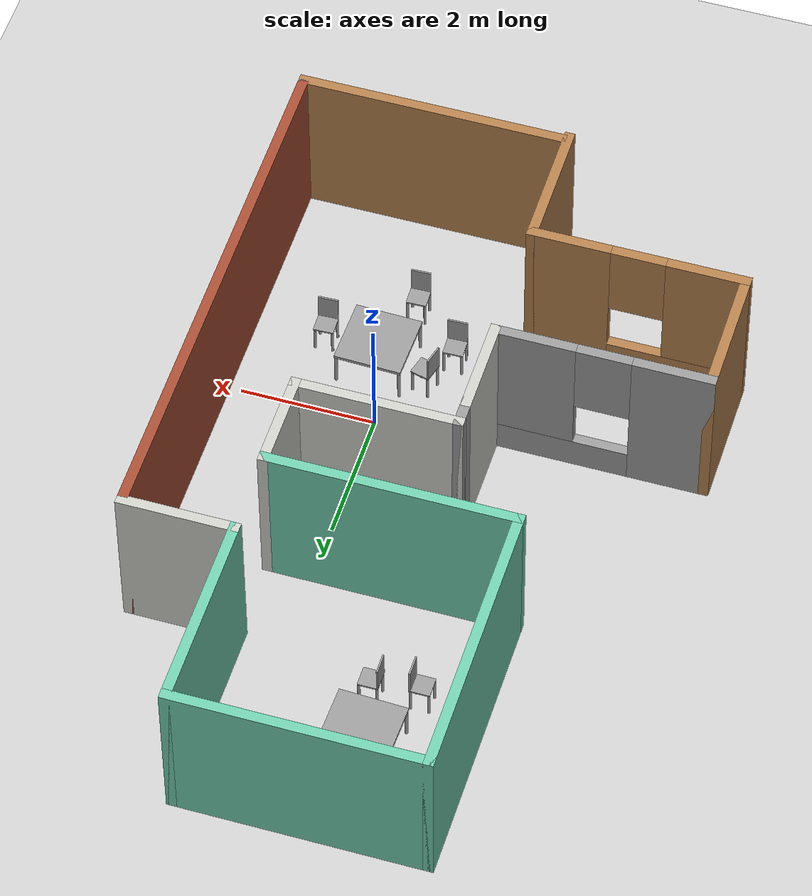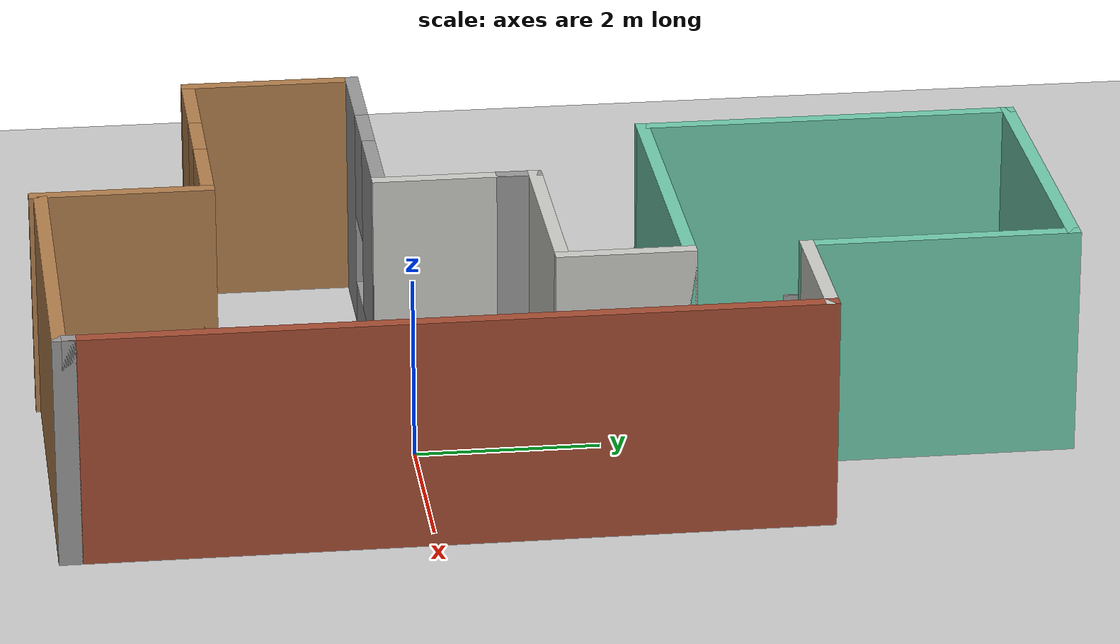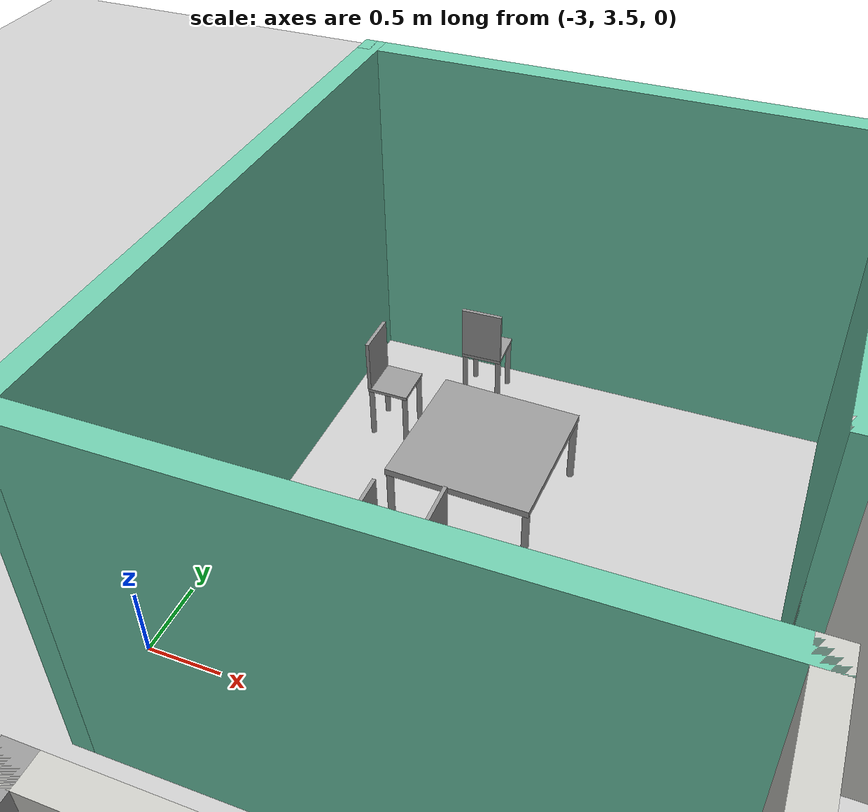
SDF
<sdf version="1.6">
 <world name="default">
  <plugin name="hello" filename="libwelcome_message.so"/>
  <light name="sun" type="directional">
   <pose>0 0 10 0 -0 0</pose>
   <diffuse>0.8 0.8 0.8 1</diffuse>
   <specular>0.2 0.2 0.2 1</specular>
   <attenuation>
    <range>1000</range>
    <constant>0.9</constant>
    <linear>0.01</linear>
    <quadratic>0.001</quadratic>
   </attenuation>
   <direction>-0.5 0.1 -0.9</direction>
  </light>
  <model name="ground_plane">
   <static>1</static>
   <link name="link">
    <collision name="collision">
     <geometry><plane><normal>0 0 1</normal><size>100 100</size></plane></geometry>
     <surface><friction><ode><mu>100</mu><mu2>50</mu2></ode></friction></surface>
    </collision>
    <visual name="visual">
     <cast_shadows>0</cast_shadows>
     <geometry><plane><normal>0 0 1</normal><size>100 100</size></plane></geometry>
     <material>
      <script><uri>file://media/materials/scripts/gazebo.material</uri><name>Gazebo/Grey</name></script>
     </material>
    </visual>
   </link>
  </model>
  <gravity>0 0 -9.8</gravity>
  <magnetic_field>6e-06 2.3e-05 -4.2e-05</magnetic_field>
  <atmosphere type="adiabatic"/>
  <physics name="default_physics" default="0" type="ode">
   <max_step_size>0.001</max_step_size>
   <real_time_factor>1</real_time_factor>
   <real_time_update_rate>1000</real_time_update_rate>
  </physics>
  <scene><ambient>0.4 0.4 0.4 1</ambient><background>0.7 0.7 0.7 1</background><shadows>1</shadows></scene>
  <spherical_coordinates>
   <surface_model>EARTH_WGS84</surface_model>
   <latitude_deg>0</latitude_deg>
   <longitude_deg>0</longitude_deg>
   <elevation>0</elevation>
   <heading_deg>0</heading_deg>
  </spherical_coordinates>
  <model name="myTable">
   <link name="link_0">
    <pose>7.65666 6.42879 0.72 0 -0 0</pose>
    <inertial>
     <mass>1</mass>
     <inertia>
      <ixx>0.166667</ixx>
      <ixy>0</ixy>
      <ixz>0</ixz>
      <iyy>0.166667</iyy>
      <iyz>0</iyz>
      <izz>0.166667</izz>
     </inertia>
    </inertial>
    <visual name="visual">
     <geometry><box><size>1 1 0.05</size></box></geometry>
     <material>
      <lighting>1</lighting>
      <script><uri>file://media/materials/scripts/gazebo.material</uri><name>Gazebo/Grey</name></script>
      <ambient>0.3 0.3 0.3 1</ambient>
      <diffuse>0.7 0.7 0.7 1</diffuse>
      <specular>0.01 0.01 0.01 1</specular>
      <emissive>0 0 0 1</emissive>
      <shader type="vertex"><normal_map>__default__</normal_map></shader>
     </material>
    </visual>
    <collision name="collision">
     <geometry><box><size>1 1 0.05</size></box></geometry>
     <surface>
      <friction>
       <ode><mu>1</mu><mu2>1</mu2><fdir1>0 0 0</fdir1><slip1>0</slip1><slip2>0</slip2></ode>
       <torsional>
        <coefficient>1</coefficient>
        <patch_radius>0</patch_radius>
        <surface_radius>0</surface_radius>
        <use_patch_radius>1</use_patch_radius>
        <ode><slip>0</slip></ode>
       </torsional>
      </friction>
      <bounce><restitution_coefficient>0</restitution_coefficient><threshold>1e+06</threshold></bounce>
      <contact>
       <collide_without_contact>0</collide_without_contact>
       <collide_without_contact_bitmask>1</collide_without_contact_bitmask>
       <collide_bitmask>1</collide_bitmask>
       <ode>
        <soft_cfm>0</soft_cfm>
        <soft_erp>0.2</soft_erp>
        <kp>1e+13</kp>
        <kd>1</kd>
        <max_vel>0.01</max_vel>
        <min_depth>0</min_depth>
       </ode>
       <bullet>
        <split_impulse>1</split_impulse>
        <split_impulse_penetration_threshold>-0.01</split_impulse_penetration_threshold>
        <soft_cfm>0</soft_cfm>
        <soft_erp>0.2</soft_erp>
        <kp>1e+13</kp>
        <kd>1</kd>
       </bullet>
      </contact>
     </surface>
    </collision>
   </link>
   <link name="link_1">
    <pose>7.18166 5.95379 0.445 0 -0 0</pose>
    <inertial>
     <mass>1</mass>
     <inertia><ixx>0.145833</ixx><ixy>0</ixy><ixz>0</ixz><iyy>0.145833</iyy><iyz>0</iyz><izz>0.125</izz></inertia>
    </inertial>
    <visual name="visual">
     <geometry><cylinder><radius>0.025</radius><length>0.5</length></cylinder></geometry>
     <material>
      <lighting>1</lighting>
      <script><uri>file://media/materials/scripts/gazebo.material</uri><name>Gazebo/Grey</name></script>
      <ambient>0.3 0.3 0.3 1</ambient>
      <diffuse>0.7 0.7 0.7 1</diffuse>
      <specular>0.01 0.01 0.01 1</specular>
      <emissive>0 0 0 1</emissive>
      <shader type="vertex"><normal_map>__default__</normal_map></shader>
     </material>
    </visual>
    <collision name="collision">
     <geometry><cylinder><radius>0.025</radius><length>0.5</length></cylinder></geometry>
     <surface>
      <friction>
       <ode><mu>1</mu><mu2>1</mu2><fdir1>0 0 0</fdir1><slip1>0</slip1><slip2>0</slip2></ode>
       <torsional>
        <coefficient>1</coefficient>
        <patch_radius>0</patch_radius>
        <surface_radius>0</surface_radius>
        <use_patch_radius>1</use_patch_radius>
        <ode><slip>0</slip></ode>
       </torsional>
      </friction>
      <bounce><restitution_coefficient>0</restitution_coefficient><threshold>1e+06</threshold></bounce>
      <contact>
       <collide_without_contact>0</collide_without_contact>
       <collide_without_contact_bitmask>1</collide_without_contact_bitmask>
       <collide_bitmask>1</collide_bitmask>
       <ode>
        <soft_cfm>0</soft_cfm>
        <soft_erp>0.2</soft_erp>
        <kp>1e+13</kp>
        <kd>1</kd>
        <max_vel>0.01</max_vel>
        <min_depth>0</min_depth>
       </ode>
       <bullet>
        <split_impulse>1</split_impulse>
        <split_impulse_penetration_threshold>-0.01</split_impulse_penetration_threshold>
        <soft_cfm>0</soft_cfm>
        <soft_erp>0.2</soft_erp>
        <kp>1e+13</kp>
        <kd>1</kd>
       </bullet>
      </contact>
     </surface>
    </collision>
   </link>
   <link name="link_1_clone">
    <pose>7.18166 6.90379 0.445 0 -0 0</pose>
    <inertial>
     <mass>1</mass>
     <inertia><ixx>0.145833</ixx><ixy>0</ixy><ixz>0</ixz><iyy>0.145833</iyy><iyz>0</iyz><izz>0.125</izz></inertia>
    </inertial>
    <visual name="visual">
     <geometry><cylinder><radius>0.025</radius><length>0.5</length></cylinder></geometry>
     <material>
      <lighting>1</lighting>
      <script><uri>file://media/materials/scripts/gazebo.material</uri><name>Gazebo/Grey</name></script>
      <ambient>0.3 0.3 0.3 1</ambient>
      <diffuse>0.7 0.7 0.7 1</diffuse>
      <specular>0.01 0.01 0.01 1</specular>
      <emissive>0 0 0 1</emissive>
      <shader type="vertex"><normal_map>__default__</normal_map></shader>
     </material>
    </visual>
    <collision name="collision">
     <geometry><cylinder><radius>0.025</radius><length>0.5</length></cylinder></geometry>
     <surface>
      <friction>
       <ode><mu>1</mu><mu2>1</mu2><fdir1>0 0 0</fdir1><slip1>0</slip1><slip2>0</slip2></ode>
       <torsional>
        <coefficient>1</coefficient>
        <patch_radius>0</patch_radius>
        <surface_radius>0</surface_radius>
        <use_patch_radius>1</use_patch_radius>
        <ode><slip>0</slip></ode>
       </torsional>
      </friction>
      <bounce><restitution_coefficient>0</restitution_coefficient><threshold>1e+06</threshold></bounce>
      <contact>
       <collide_without_contact>0</collide_without_contact>
       <collide_without_contact_bitmask>1</collide_without_contact_bitmask>
       <collide_bitmask>1</collide_bitmask>
       <ode>
        <soft_cfm>0</soft_cfm>
        <soft_erp>0.2</soft_erp>
        <kp>1e+13</kp>
        <kd>1</kd>
        <max_vel>0.01</max_vel>
        <min_depth>0</min_depth>
       </ode>
       <bullet>
        <split_impulse>1</split_impulse>
        <split_impulse_penetration_threshold>-0.01</split_impulse_penetration_threshold>
        <soft_cfm>0</soft_cfm>
        <soft_erp>0.2</soft_erp>
        <kp>1e+13</kp>
        <kd>1</kd>
       </bullet>
      </contact>
     </surface>
    </collision>
   </link>
   <link name="link_1_clone_0">
    <pose>8.13166 6.90379 0.445 0 -0 0</pose>
    <inertial>
     <mass>1</mass>
     <inertia><ixx>0.145833</ixx><ixy>0</ixy><ixz>0</ixz><iyy>0.145833</iyy><iyz>0</iyz><izz>0.125</izz></inertia>
    </inertial>
    <visual name="visual">
     <geometry><cylinder><radius>0.025</radius><length>0.5</length></cylinder></geometry>
     <material>
      <lighting>1</lighting>
      <script><uri>file://media/materials/scripts/gazebo.material</uri><name>Gazebo/Grey</name></script>
      <ambient>0.3 0.3 0.3 1</ambient>
      <diffuse>0.7 0.7 0.7 1</diffuse>
      <specular>0.01 0.01 0.01 1</specular>
      <emissive>0 0 0 1</emissive>
      <shader type="vertex"><normal_map>__default__</normal_map></shader>
     </material>
    </visual>
    <collision name="collision">
     <geometry><cylinder><radius>0.025</radius><length>0.5</length></cylinder></geometry>
     <surface>
      <friction>
       <ode><mu>1</mu><mu2>1</mu2><fdir1>0 0 0</fdir1><slip1>0</slip1><slip2>0</slip2></ode>
       <torsional>
        <coefficient>1</coefficient>
        <patch_radius>0</patch_radius>
        <surface_radius>0</surface_radius>
        <use_patch_radius>1</use_patch_radius>
        <ode><slip>0</slip></ode>
       </torsional>
      </friction>
      <bounce><restitution_coefficient>0</restitution_coefficient><threshold>1e+06</threshold></bounce>
      <contact>
       <collide_without_contact>0</collide_without_contact>
       <collide_without_contact_bitmask>1</collide_without_contact_bitmask>
       <collide_bitmask>1</collide_bitmask>
       <ode>
        <soft_cfm>0</soft_cfm>
        <soft_erp>0.2</soft_erp>
        <kp>1e+13</kp>
        <kd>1</kd>
        <max_vel>0.01</max_vel>
        <min_depth>0</min_depth>
       </ode>
       <bullet>
        <split_impulse>1</split_impulse>
        <split_impulse_penetration_threshold>-0.01</split_impulse_penetration_threshold>
        <soft_cfm>0</soft_cfm>
        <soft_erp>0.2</soft_erp>
        <kp>1e+13</kp>
        <kd>1</kd>
       </bullet>
      </contact>
     </surface>
    </collision>
   </link>
   <link name="link_1_clone_1">
    <pose>8.13166 5.95379 0.445 0 -0 0</pose>
    <inertial>
     <mass>1</mass>
     <inertia><ixx>0.145833</ixx><ixy>0</ixy><ixz>0</ixz><iyy>0.145833</iyy><iyz>0</iyz><izz>0.125</izz></inertia>
    </inertial>
    <visual name="visual">
     <geometry><cylinder><radius>0.025</radius><length>0.5</length></cylinder></geometry>
     <material>
      <lighting>1</lighting>
      <script><uri>file://media/materials/scripts/gazebo.material</uri><name>Gazebo/Grey</name></script>
      <ambient>0.3 0.3 0.3 1</ambient>
      <diffuse>0.7 0.7 0.7 1</diffuse>
      <specular>0.01 0.01 0.01 1</specular>
      <emissive>0 0 0 1</emissive>
      <shader type="vertex"><normal_map>__default__</normal_map></shader>
     </material>
    </visual>
    <collision name="collision">
     <geometry><cylinder><radius>0.025</radius><length>0.5</length></cylinder></geometry>
     <surface>
      <friction>
       <ode><mu>1</mu><mu2>1</mu2><fdir1>0 0 0</fdir1><slip1>0</slip1><slip2>0</slip2></ode>
       <torsional>
        <coefficient>1</coefficient>
        <patch_radius>0</patch_radius>
        <surface_radius>0</surface_radius>
        <use_patch_radius>1</use_patch_radius>
        <ode><slip>0</slip></ode>
       </torsional>
      </friction>
      <bounce><restitution_coefficient>0</restitution_coefficient><threshold>1e+06</threshold></bounce>
      <contact>
       <collide_without_contact>0</collide_without_contact>
       <collide_without_contact_bitmask>1</collide_without_contact_bitmask>
       <collide_bitmask>1</collide_bitmask>
       <ode>
        <soft_cfm>0</soft_cfm>
        <soft_erp>0.2</soft_erp>
        <kp>1e+13</kp>
        <kd>1</kd>
        <max_vel>0.01</max_vel>
        <min_depth>0</min_depth>
       </ode>
       <bullet>
        <split_impulse>1</split_impulse>
        <split_impulse_penetration_threshold>-0.01</split_impulse_penetration_threshold>
        <soft_cfm>0</soft_cfm>
        <soft_erp>0.2</soft_erp>
        <kp>1e+13</kp>
        <kd>1</kd>
       </bullet>
      </contact>
     </surface>
    </collision>
   </link>
   <joint name="link_0_JOINT_0" type="fixed">
    <parent>link_0</parent>
    <child>link_1</child>
    <physics>
     <ode><limit><cfm>0</cfm><erp>0.2</erp></limit><suspension><cfm>0</cfm><erp>0.2</erp></suspension></ode>
    </physics>
   </joint>
   <joint name="link_0_JOINT_1" type="fixed">
    <parent>link_0</parent>
    <child>link_1_clone_1</child>
    <physics>
     <ode><limit><cfm>0</cfm><erp>0.2</erp></limit><suspension><cfm>0</cfm><erp>0.2</erp></suspension></ode>
    </physics>
   </joint>
   <joint name="link_0_JOINT_2" type="revolute">
    <parent>link_0</parent>
    <child>link_1_clone</child>
    <axis>
     <xyz>1 0 0</xyz>
     <use_parent_model_frame>0</use_parent_model_frame>
     <limit>
      <lower>-1.79769e+308</lower>
      <upper>1.79769e+308</upper>
      <effort>-1</effort>
      <velocity>-1</velocity>
     </limit>
     <dynamics>
      <spring_reference>0</spring_reference>
      <spring_stiffness>0</spring_stiffness>
      <damping>0</damping>
     </dynamics>
    </axis>
    <physics>
     <ode><limit><cfm>0</cfm><erp>0.2</erp></limit><suspension><cfm>0</cfm><erp>0.2</erp></suspension></ode>
    </physics>
   </joint>
   <joint name="link_0_JOINT_3" type="fixed">
    <parent>link_0</parent>
    <child>link_1_clone_0</child>
    <physics>
     <ode><limit><cfm>0</cfm><erp>0.2</erp></limit><suspension><cfm>0</cfm><erp>0.2</erp></suspension></ode>
    </physics>
   </joint>
   <static>0</static>
   <pose>-9.39862 -0.736906 -0.195 7e-06 6e-06 -0.033007</pose>
  </model>
  <model name="myTable_0">
   <link name="link_0">
    <pose>7.65666 6.42879 0.72 0 -0 0</pose>
    <inertial>
     <mass>1</mass>
     <inertia>
      <ixx>0.166667</ixx>
      <ixy>0</ixy>
      <ixz>0</ixz>
      <iyy>0.166667</iyy>
      <iyz>0</iyz>
      <izz>0.166667</izz>
     </inertia>
    </inertial>
    <visual name="visual">
     <geometry><box><size>1 1 0.05</size></box></geometry>
     <material>
      <lighting>1</lighting>
      <script><uri>file://media/materials/scripts/gazebo.material</uri><name>Gazebo/Grey</name></script>
      <ambient>0.3 0.3 0.3 1</ambient>
      <diffuse>0.7 0.7 0.7 1</diffuse>
      <specular>0.01 0.01 0.01 1</specular>
      <emissive>0 0 0 1</emissive>
      <shader type="vertex"><normal_map>__default__</normal_map></shader>
     </material>
    </visual>
    <collision name="collision">
     <geometry><box><size>1 1 0.05</size></box></geometry>
     <surface>
      <friction>
       <ode><mu>1</mu><mu2>1</mu2><fdir1>0 0 0</fdir1><slip1>0</slip1><slip2>0</slip2></ode>
       <torsional>
        <coefficient>1</coefficient>
        <patch_radius>0</patch_radius>
        <surface_radius>0</surface_radius>
        <use_patch_radius>1</use_patch_radius>
        <ode><slip>0</slip></ode>
       </torsional>
      </friction>
      <bounce><restitution_coefficient>0</restitution_coefficient><threshold>1e+06</threshold></bounce>
      <contact>
       <collide_without_contact>0</collide_without_contact>
       <collide_without_contact_bitmask>1</collide_without_contact_bitmask>
       <collide_bitmask>1</collide_bitmask>
       <ode>
        <soft_cfm>0</soft_cfm>
        <soft_erp>0.2</soft_erp>
        <kp>1e+13</kp>
        <kd>1</kd>
        <max_vel>0.01</max_vel>
        <min_depth>0</min_depth>
       </ode>
       <bullet>
        <split_impulse>1</split_impulse>
        <split_impulse_penetration_threshold>-0.01</split_impulse_penetration_threshold>
        <soft_cfm>0</soft_cfm>
        <soft_erp>0.2</soft_erp>
        <kp>1e+13</kp>
        <kd>1</kd>
       </bullet>
      </contact>
     </surface>
    </collision>
   </link>
   <link name="link_1">
    <pose>7.18166 5.95379 0.445 0 -0 0</pose>
    <inertial>
     <mass>1</mass>
     <inertia><ixx>0.145833</ixx><ixy>0</ixy><ixz>0</ixz><iyy>0.145833</iyy><iyz>0</iyz><izz>0.125</izz></inertia>
    </inertial>
    <visual name="visual">
     <geometry><cylinder><radius>0.025</radius><length>0.5</length></cylinder></geometry>
     <material>
      <lighting>1</lighting>
      <script><uri>file://media/materials/scripts/gazebo.material</uri><name>Gazebo/Grey</name></script>
      <ambient>0.3 0.3 0.3 1</ambient>
      <diffuse>0.7 0.7 0.7 1</diffuse>
      <specular>0.01 0.01 0.01 1</specular>
      <emissive>0 0 0 1</emissive>
      <shader type="vertex"><normal_map>__default__</normal_map></shader>
     </material>
    </visual>
    <collision name="collision">
     <geometry><cylinder><radius>0.025</radius><length>0.5</length></cylinder></geometry>
     <surface>
      <friction>
       <ode><mu>1</mu><mu2>1</mu2><fdir1>0 0 0</fdir1><slip1>0</slip1><slip2>0</slip2></ode>
       <torsional>
        <coefficient>1</coefficient>
        <patch_radius>0</patch_radius>
        <surface_radius>0</surface_radius>
        <use_patch_radius>1</use_patch_radius>
        <ode><slip>0</slip></ode>
       </torsional>
      </friction>
      <bounce><restitution_coefficient>0</restitution_coefficient><threshold>1e+06</threshold></bounce>
      <contact>
       <collide_without_contact>0</collide_without_contact>
       <collide_without_contact_bitmask>1</collide_without_contact_bitmask>
       <collide_bitmask>1</collide_bitmask>
       <ode>
        <soft_cfm>0</soft_cfm>
        <soft_erp>0.2</soft_erp>
        <kp>1e+13</kp>
        <kd>1</kd>
        <max_vel>0.01</max_vel>
        <min_depth>0</min_depth>
       </ode>
       <bullet>
        <split_impulse>1</split_impulse>
        <split_impulse_penetration_threshold>-0.01</split_impulse_penetration_threshold>
        <soft_cfm>0</soft_cfm>
        <soft_erp>0.2</soft_erp>
        <kp>1e+13</kp>
        <kd>1</kd>
       </bullet>
      </contact>
     </surface>
    </collision>
   </link>
   <link name="link_1_clone">
    <pose>7.18166 6.90379 0.445 0 -0 0</pose>
    <inertial>
     <mass>1</mass>
     <inertia><ixx>0.145833</ixx><ixy>0</ixy><ixz>0</ixz><iyy>0.145833</iyy><iyz>0</iyz><izz>0.125</izz></inertia>
    </inertial>
    <visual name="visual">
     <geometry><cylinder><radius>0.025</radius><length>0.5</length></cylinder></geometry>
     <material>
      <lighting>1</lighting>
      <script><uri>file://media/materials/scripts/gazebo.material</uri><name>Gazebo/Grey</name></script>
      <ambient>0.3 0.3 0.3 1</ambient>
      <diffuse>0.7 0.7 0.7 1</diffuse>
      <specular>0.01 0.01 0.01 1</specular>
      <emissive>0 0 0 1</emissive>
      <shader type="vertex"><normal_map>__default__</normal_map></shader>
     </material>
    </visual>
    <collision name="collision">
     <geometry><cylinder><radius>0.025</radius><length>0.5</length></cylinder></geometry>
     <surface>
      <friction>
       <ode><mu>1</mu><mu2>1</mu2><fdir1>0 0 0</fdir1><slip1>0</slip1><slip2>0</slip2></ode>
       <torsional>
        <coefficient>1</coefficient>
        <patch_radius>0</patch_radius>
        <surface_radius>0</surface_radius>
        <use_patch_radius>1</use_patch_radius>
        <ode><slip>0</slip></ode>
       </torsional>
      </friction>
      <bounce><restitution_coefficient>0</restitution_coefficient><threshold>1e+06</threshold></bounce>
      <contact>
       <collide_without_contact>0</collide_without_contact>
       <collide_without_contact_bitmask>1</collide_without_contact_bitmask>
       <collide_bitmask>1</collide_bitmask>
       <ode>
        <soft_cfm>0</soft_cfm>
        <soft_erp>0.2</soft_erp>
        <kp>1e+13</kp>
        <kd>1</kd>
        <max_vel>0.01</max_vel>
        <min_depth>0</min_depth>
       </ode>
       <bullet>
        <split_impulse>1</split_impulse>
        <split_impulse_penetration_threshold>-0.01</split_impulse_penetration_threshold>
        <soft_cfm>0</soft_cfm>
        <soft_erp>0.2</soft_erp>
        <kp>1e+13</kp>
        <kd>1</kd>
       </bullet>
      </contact>
     </surface>
    </collision>
   </link>
   <link name="link_1_clone_0">
    <pose>8.13166 6.90379 0.445 0 -0 0</pose>
    <inertial>
     <mass>1</mass>
     <inertia><ixx>0.145833</ixx><ixy>0</ixy><ixz>0</ixz><iyy>0.145833</iyy><iyz>0</iyz><izz>0.125</izz></inertia>
    </inertial>
    <visual name="visual">
     <geometry><cylinder><radius>0.025</radius><length>0.5</length></cylinder></geometry>
     <material>
      <lighting>1</lighting>
      <script><uri>file://media/materials/scripts/gazebo.material</uri><name>Gazebo/Grey</name></script>
      <ambient>0.3 0.3 0.3 1</ambient>
      <diffuse>0.7 0.7 0.7 1</diffuse>
      <specular>0.01 0.01 0.01 1</specular>
      <emissive>0 0 0 1</emissive>
      <shader type="vertex"><normal_map>__default__</normal_map></shader>
     </material>
    </visual>
    <collision name="collision">
     <geometry><cylinder><radius>0.025</radius><length>0.5</length></cylinder></geometry>
     <surface>
      <friction>
       <ode><mu>1</mu><mu2>1</mu2><fdir1>0 0 0</fdir1><slip1>0</slip1><slip2>0</slip2></ode>
       <torsional>
        <coefficient>1</coefficient>
        <patch_radius>0</patch_radius>
        <surface_radius>0</surface_radius>
        <use_patch_radius>1</use_patch_radius>
        <ode><slip>0</slip></ode>
       </torsional>
      </friction>
      <bounce><restitution_coefficient>0</restitution_coefficient><threshold>1e+06</threshold></bounce>
      <contact>
       <collide_without_contact>0</collide_without_contact>
       <collide_without_contact_bitmask>1</collide_without_contact_bitmask>
       <collide_bitmask>1</collide_bitmask>
       <ode>
        <soft_cfm>0</soft_cfm>
        <soft_erp>0.2</soft_erp>
        <kp>1e+13</kp>
        <kd>1</kd>
        <max_vel>0.01</max_vel>
        <min_depth>0</min_depth>
       </ode>
       <bullet>
        <split_impulse>1</split_impulse>
        <split_impulse_penetration_threshold>-0.01</split_impulse_penetration_threshold>
        <soft_cfm>0</soft_cfm>
        <soft_erp>0.2</soft_erp>
        <kp>1e+13</kp>
        <kd>1</kd>
       </bullet>
      </contact>
     </surface>
    </collision>
   </link>
   <link name="link_1_clone_1">
    <pose>8.13166 5.95379 0.445 0 -0 0</pose>
    <inertial>
     <mass>1</mass>
     <inertia><ixx>0.145833</ixx><ixy>0</ixy><ixz>0</ixz><iyy>0.145833</iyy><iyz>0</iyz><izz>0.125</izz></inertia>
    </inertial>
    <visual name="visual">
     <geometry><cylinder><radius>0.025</radius><length>0.5</length></cylinder></geometry>
     <material>
      <lighting>1</lighting>
      <script><uri>file://media/materials/scripts/gazebo.material</uri><name>Gazebo/Grey</name></script>
      <ambient>0.3 0.3 0.3 1</ambient>
      <diffuse>0.7 0.7 0.7 1</diffuse>
      <specular>0.01 0.01 0.01 1</specular>
      <emissive>0 0 0 1</emissive>
      <shader type="vertex"><normal_map>__default__</normal_map></shader>
     </material>
    </visual>
    <collision name="collision">
     <geometry><cylinder><radius>0.025</radius><length>0.5</length></cylinder></geometry>
     <surface>
      <friction>
       <ode><mu>1</mu><mu2>1</mu2><fdir1>0 0 0</fdir1><slip1>0</slip1><slip2>0</slip2></ode>
       <torsional>
        <coefficient>1</coefficient>
        <patch_radius>0</patch_radius>
        <surface_radius>0</surface_radius>
        <use_patch_radius>1</use_patch_radius>
        <ode><slip>0</slip></ode>
       </torsional>
      </friction>
      <bounce><restitution_coefficient>0</restitution_coefficient><threshold>1e+06</threshold></bounce>
      <contact>
       <collide_without_contact>0</collide_without_contact>
       <collide_without_contact_bitmask>1</collide_without_contact_bitmask>
       <collide_bitmask>1</collide_bitmask>
       <ode>
        <soft_cfm>0</soft_cfm>
        <soft_erp>0.2</soft_erp>
        <kp>1e+13</kp>
        <kd>1</kd>
        <max_vel>0.01</max_vel>
        <min_depth>0</min_depth>
       </ode>
       <bullet>
        <split_impulse>1</split_impulse>
        <split_impulse_penetration_threshold>-0.01</split_impulse_penetration_threshold>
        <soft_cfm>0</soft_cfm>
        <soft_erp>0.2</soft_erp>
        <kp>1e+13</kp>
        <kd>1</kd>
       </bullet>
      </contact>
     </surface>
    </collision>
   </link>
   <joint name="link_0_JOINT_0" type="fixed">
    <parent>link_0</parent>
    <child>link_1</child>
    <physics>
     <ode><limit><cfm>0</cfm><erp>0.2</erp></limit><suspension><cfm>0</cfm><erp>0.2</erp></suspension></ode>
    </physics>
   </joint>
   <joint name="link_0_JOINT_1" type="fixed">
    <parent>link_0</parent>
    <child>link_1_clone_1</child>
    <physics>
     <ode><limit><cfm>0</cfm><erp>0.2</erp></limit><suspension><cfm>0</cfm><erp>0.2</erp></suspension></ode>
    </physics>
   </joint>
   <joint name="link_0_JOINT_2" type="revolute">
    <parent>link_0</parent>
    <child>link_1_clone</child>
    <axis>
     <xyz>1 0 0</xyz>
     <use_parent_model_frame>0</use_parent_model_frame>
     <limit>
      <lower>-1.79769e+308</lower>
      <upper>1.79769e+308</upper>
      <effort>-1</effort>
      <velocity>-1</velocity>
     </limit>
     <dynamics>
      <spring_reference>0</spring_reference>
      <spring_stiffness>0</spring_stiffness>
      <damping>0</damping>
     </dynamics>
    </axis>
    <physics>
     <ode><limit><cfm>0</cfm><erp>0.2</erp></limit><suspension><cfm>0</cfm><erp>0.2</erp></suspension></ode>
    </physics>
   </joint>
   <joint name="link_0_JOINT_3" type="fixed">
    <parent>link_0</parent>
    <child>link_1_clone_0</child>
    <physics>
     <ode><limit><cfm>0</cfm><erp>0.2</erp></limit><suspension><cfm>0</cfm><erp>0.2</erp></suspension></ode>
    </physics>
   </joint>
   <static>0</static>
   <pose>-7.5568 -7.28185 -0.195003 1e-05 8e-06 -0.027451</pose>
  </model>
  <model name="myChair">
   <link name="link_0">
    <pose>0.022917 -0 0.0914 0 -0 0</pose>
    <inertial>
     <mass>1</mass>
     <inertia>
      <ixx>0.166667</ixx>
      <ixy>0</ixy>
      <ixz>0</ixz>
      <iyy>0.166667</iyy>
      <iyz>0</iyz>
      <izz>0.166667</izz>
     </inertia>
    </inertial>
    <visual name="visual">
     <geometry><box><size>0.3 0.3 0.025</size></box></geometry>
     <material>
      <lighting>1</lighting>
      <script><uri>file://media/materials/scripts/gazebo.material</uri><name>Gazebo/Grey</name></script>
      <ambient>0.3 0.3 0.3 1</ambient>
      <diffuse>0.7 0.7 0.7 1</diffuse>
      <specular>0.01 0.01 0.01 1</specular>
      <emissive>0 0 0 1</emissive>
      <shader type="vertex"><normal_map>__default__</normal_map></shader>
     </material>
    </visual>
    <collision name="collision">
     <geometry><box><size>0.3 0.3 0.025</size></box></geometry>
     <surface>
      <friction>
       <ode><mu>1</mu><mu2>1</mu2><fdir1>0 0 0</fdir1><slip1>0</slip1><slip2>0</slip2></ode>
       <torsional>
        <coefficient>1</coefficient>
        <patch_radius>0</patch_radius>
        <surface_radius>0</surface_radius>
        <use_patch_radius>1</use_patch_radius>
        <ode><slip>0</slip></ode>
       </torsional>
      </friction>
      <bounce><restitution_coefficient>0</restitution_coefficient><threshold>1e+06</threshold></bounce>
      <contact>
       <collide_without_contact>0</collide_without_contact>
       <collide_without_contact_bitmask>1</collide_without_contact_bitmask>
       <collide_bitmask>1</collide_bitmask>
       <ode>
        <soft_cfm>0</soft_cfm>
        <soft_erp>0.2</soft_erp>
        <kp>1e+13</kp>
        <kd>1</kd>
        <max_vel>0.01</max_vel>
        <min_depth>0</min_depth>
       </ode>
       <bullet>
        <split_impulse>1</split_impulse>
        <split_impulse_penetration_threshold>-0.01</split_impulse_penetration_threshold>
        <soft_cfm>0</soft_cfm>
        <soft_erp>0.2</soft_erp>
        <kp>1e+13</kp>
        <kd>1</kd>
       </bullet>
      </contact>
     </surface>
    </collision>
   </link>
   <link name="link_1">
    <pose>-0.107083 -0.13 -0.11875 0 -0 0</pose>
    <inertial>
     <mass>1</mass>
     <inertia><ixx>0.145833</ixx><ixy>0</ixy><ixz>0</ixz><iyy>0.145833</iyy><iyz>0</iyz><izz>0.125</izz></inertia>
    </inertial>
    <visual name="visual">
     <geometry><cylinder><radius>0.02</radius><length>0.4</length></cylinder></geometry>
     <material>
      <lighting>1</lighting>
      <script><uri>file://media/materials/scripts/gazebo.material</uri><name>Gazebo/Grey</name></script>
      <ambient>0.3 0.3 0.3 1</ambient>
      <diffuse>0.7 0.7 0.7 1</diffuse>
      <specular>0.01 0.01 0.01 1</specular>
      <emissive>0 0 0 1</emissive>
      <shader type="vertex"><normal_map>__default__</normal_map></shader>
     </material>
    </visual>
    <collision name="collision">
     <geometry><cylinder><radius>0.02</radius><length>0.4</length></cylinder></geometry>
     <surface>
      <friction>
       <ode><mu>1</mu><mu2>1</mu2><fdir1>0 0 0</fdir1><slip1>0</slip1><slip2>0</slip2></ode>
       <torsional>
        <coefficient>1</coefficient>
        <patch_radius>0</patch_radius>
        <surface_radius>0</surface_radius>
        <use_patch_radius>1</use_patch_radius>
        <ode><slip>0</slip></ode>
       </torsional>
      </friction>
      <bounce><restitution_coefficient>0</restitution_coefficient><threshold>1e+06</threshold></bounce>
      <contact>
       <collide_without_contact>0</collide_without_contact>
       <collide_without_contact_bitmask>1</collide_without_contact_bitmask>
       <collide_bitmask>1</collide_bitmask>
       <ode>
        <soft_cfm>0</soft_cfm>
        <soft_erp>0.2</soft_erp>
        <kp>1e+13</kp>
        <kd>1</kd>
        <max_vel>0.01</max_vel>
        <min_depth>0</min_depth>
       </ode>
       <bullet>
        <split_impulse>1</split_impulse>
        <split_impulse_penetration_threshold>-0.01</split_impulse_penetration_threshold>
        <soft_cfm>0</soft_cfm>
        <soft_erp>0.2</soft_erp>
        <kp>1e+13</kp>
        <kd>1</kd>
       </bullet>
      </contact>
     </surface>
    </collision>
   </link>
   <link name="link_1_clone">
    <pose>-0.107083 0.13 -0.11875 0 -0 0</pose>
    <inertial>
     <mass>1</mass>
     <inertia><ixx>0.145833</ixx><ixy>0</ixy><ixz>0</ixz><iyy>0.145833</iyy><iyz>0</iyz><izz>0.125</izz></inertia>
    </inertial>
    <visual name="visual">
     <geometry><cylinder><radius>0.02</radius><length>0.4</length></cylinder></geometry>
     <material>
      <lighting>1</lighting>
      <script><uri>file://media/materials/scripts/gazebo.material</uri><name>Gazebo/Grey</name></script>
      <ambient>0.3 0.3 0.3 1</ambient>
      <diffuse>0.7 0.7 0.7 1</diffuse>
      <specular>0.01 0.01 0.01 1</specular>
      <emissive>0 0 0 1</emissive>
      <shader type="vertex"><normal_map>__default__</normal_map></shader>
     </material>
    </visual>
    <collision name="collision">
     <geometry><cylinder><radius>0.02</radius><length>0.4</length></cylinder></geometry>
     <surface>
      <friction>
       <ode><mu>1</mu><mu2>1</mu2><fdir1>0 0 0</fdir1><slip1>0</slip1><slip2>0</slip2></ode>
       <torsional>
        <coefficient>1</coefficient>
        <patch_radius>0</patch_radius>
        <surface_radius>0</surface_radius>
        <use_patch_radius>1</use_patch_radius>
        <ode><slip>0</slip></ode>
       </torsional>
      </friction>
      <bounce><restitution_coefficient>0</restitution_coefficient><threshold>1e+06</threshold></bounce>
      <contact>
       <collide_without_contact>0</collide_without_contact>
       <collide_without_contact_bitmask>1</collide_without_contact_bitmask>
       <collide_bitmask>1</collide_bitmask>
       <ode>
        <soft_cfm>0</soft_cfm>
        <soft_erp>0.2</soft_erp>
        <kp>1e+13</kp>
        <kd>1</kd>
        <max_vel>0.01</max_vel>
        <min_depth>0</min_depth>
       </ode>
       <bullet>
        <split_impulse>1</split_impulse>
        <split_impulse_penetration_threshold>-0.01</split_impulse_penetration_threshold>
        <soft_cfm>0</soft_cfm>
        <soft_erp>0.2</soft_erp>
        <kp>1e+13</kp>
        <kd>1</kd>
       </bullet>
      </contact>
     </surface>
    </collision>
   </link>
   <link name="link_1_clone_0">
    <pose>0.152917 -0.13 -0.11875 0 -0 0</pose>
    <inertial>
     <mass>1</mass>
     <inertia><ixx>0.145833</ixx><ixy>0</ixy><ixz>0</ixz><iyy>0.145833</iyy><iyz>0</iyz><izz>0.125</izz></inertia>
    </inertial>
    <visual name="visual">
     <geometry><cylinder><radius>0.02</radius><length>0.4</length></cylinder></geometry>
     <material>
      <lighting>1</lighting>
      <script><uri>file://media/materials/scripts/gazebo.material</uri><name>Gazebo/Grey</name></script>
      <ambient>0.3 0.3 0.3 1</ambient>
      <diffuse>0.7 0.7 0.7 1</diffuse>
      <specular>0.01 0.01 0.01 1</specular>
      <emissive>0 0 0 1</emissive>
      <shader type="vertex"><normal_map>__default__</normal_map></shader>
     </material>
    </visual>
    <collision name="collision">
     <geometry><cylinder><radius>0.02</radius><length>0.4</length></cylinder></geometry>
     <surface>
      <friction>
       <ode><mu>1</mu><mu2>1</mu2><fdir1>0 0 0</fdir1><slip1>0</slip1><slip2>0</slip2></ode>
       <torsional>
        <coefficient>1</coefficient>
        <patch_radius>0</patch_radius>
        <surface_radius>0</surface_radius>
        <use_patch_radius>1</use_patch_radius>
        <ode><slip>0</slip></ode>
       </torsional>
      </friction>
      <bounce><restitution_coefficient>0</restitution_coefficient><threshold>1e+06</threshold></bounce>
      <contact>
       <collide_without_contact>0</collide_without_contact>
       <collide_without_contact_bitmask>1</collide_without_contact_bitmask>
       <collide_bitmask>1</collide_bitmask>
       <ode>
        <soft_cfm>0</soft_cfm>
        <soft_erp>0.2</soft_erp>
        <kp>1e+13</kp>
        <kd>1</kd>
        <max_vel>0.01</max_vel>
        <min_depth>0</min_depth>
       </ode>
       <bullet>
        <split_impulse>1</split_impulse>
        <split_impulse_penetration_threshold>-0.01</split_impulse_penetration_threshold>
        <soft_cfm>0</soft_cfm>
        <soft_erp>0.2</soft_erp>
        <kp>1e+13</kp>
        <kd>1</kd>
       </bullet>
      </contact>
     </surface>
    </collision>
   </link>
   <link name="link_1_clone_1">
    <pose>0.152917 0.13 -0.11875 0 -0 0</pose>
    <inertial>
     <mass>1</mass>
     <inertia><ixx>0.145833</ixx><ixy>0</ixy><ixz>0</ixz><iyy>0.145833</iyy><iyz>0</iyz><izz>0.125</izz></inertia>
    </inertial>
    <visual name="visual">
     <geometry><cylinder><radius>0.02</radius><length>0.4</length></cylinder></geometry>
     <material>
      <lighting>1</lighting>
      <script><uri>file://media/materials/scripts/gazebo.material</uri><name>Gazebo/Grey</name></script>
      <ambient>0.3 0.3 0.3 1</ambient>
      <diffuse>0.7 0.7 0.7 1</diffuse>
      <specular>0.01 0.01 0.01 1</specular>
      <emissive>0 0 0 1</emissive>
      <shader type="vertex"><normal_map>__default__</normal_map></shader>
     </material>
    </visual>
    <collision name="collision">
     <geometry><cylinder><radius>0.02</radius><length>0.4</length></cylinder></geometry>
     <surface>
      <friction>
       <ode><mu>1</mu><mu2>1</mu2><fdir1>0 0 0</fdir1><slip1>0</slip1><slip2>0</slip2></ode>
       <torsional>
        <coefficient>1</coefficient>
        <patch_radius>0</patch_radius>
        <surface_radius>0</surface_radius>
        <use_patch_radius>1</use_patch_radius>
        <ode><slip>0</slip></ode>
       </torsional>
      </friction>
      <bounce><restitution_coefficient>0</restitution_coefficient><threshold>1e+06</threshold></bounce>
      <contact>
       <collide_without_contact>0</collide_without_contact>
       <collide_without_contact_bitmask>1</collide_without_contact_bitmask>
       <collide_bitmask>1</collide_bitmask>
       <ode>
        <soft_cfm>0</soft_cfm>
        <soft_erp>0.2</soft_erp>
        <kp>1e+13</kp>
        <kd>1</kd>
        <max_vel>0.01</max_vel>
        <min_depth>0</min_depth>
       </ode>
       <bullet>
        <split_impulse>1</split_impulse>
        <split_impulse_penetration_threshold>-0.01</split_impulse_penetration_threshold>
        <soft_cfm>0</soft_cfm>
        <soft_erp>0.2</soft_erp>
        <kp>1e+13</kp>
        <kd>1</kd>
       </bullet>
      </contact>
     </surface>
    </collision>
   </link>
   <link name="link_2">
    <pose>-0.114583 0 0.303495 0 -0 0</pose>
    <inertial>
     <mass>1</mass>
     <inertia>
      <ixx>0.166667</ixx>
      <ixy>0</ixy>
      <ixz>0</ixz>
      <iyy>0.166667</iyy>
      <iyz>0</iyz>
      <izz>0.166667</izz>
     </inertia>
    </inertial>
    <visual name="visual">
     <geometry><box><size>0.025 0.3 0.4</size></box></geometry>
     <material>
      <lighting>1</lighting>
      <script><uri>file://media/materials/scripts/gazebo.material</uri><name>Gazebo/Grey</name></script>
      <ambient>0.3 0.3 0.3 1</ambient>
      <diffuse>0.7 0.7 0.7 1</diffuse>
      <specular>0.01 0.01 0.01 1</specular>
      <emissive>0 0 0 1</emissive>
      <shader type="vertex"><normal_map>__default__</normal_map></shader>
     </material>
    </visual>
    <collision name="collision">
     <geometry><box><size>0.025 0.3 0.4</size></box></geometry>
     <surface>
      <friction>
       <ode><mu>1</mu><mu2>1</mu2><fdir1>0 0 0</fdir1><slip1>0</slip1><slip2>0</slip2></ode>
       <torsional>
        <coefficient>1</coefficient>
        <patch_radius>0</patch_radius>
        <surface_radius>0</surface_radius>
        <use_patch_radius>1</use_patch_radius>
        <ode><slip>0</slip></ode>
       </torsional>
      </friction>
      <bounce><restitution_coefficient>0</restitution_coefficient><threshold>1e+06</threshold></bounce>
      <contact>
       <collide_without_contact>0</collide_without_contact>
       <collide_without_contact_bitmask>1</collide_without_contact_bitmask>
       <collide_bitmask>1</collide_bitmask>
       <ode>
        <soft_cfm>0</soft_cfm>
        <soft_erp>0.2</soft_erp>
        <kp>1e+13</kp>
        <kd>1</kd>
        <max_vel>0.01</max_vel>
        <min_depth>0</min_depth>
       </ode>
       <bullet>
        <split_impulse>1</split_impulse>
        <split_impulse_penetration_threshold>-0.01</split_impulse_penetration_threshold>
        <soft_cfm>0</soft_cfm>
        <soft_erp>0.2</soft_erp>
        <kp>1e+13</kp>
        <kd>1</kd>
       </bullet>
      </contact>
     </surface>
    </collision>
   </link>
   <joint name="link_0_JOINT_0" type="fixed">
    <parent>link_0</parent>
    <child>link_1</child>
    <physics>
     <ode><limit><cfm>0</cfm><erp>0.2</erp></limit><suspension><cfm>0</cfm><erp>0.2</erp></suspension></ode>
    </physics>
   </joint>
   <joint name="link_0_JOINT_1" type="fixed">
    <parent>link_0</parent>
    <child>link_1_clone</child>
    <physics>
     <ode><limit><cfm>0</cfm><erp>0.2</erp></limit><suspension><cfm>0</cfm><erp>0.2</erp></suspension></ode>
    </physics>
   </joint>
   <joint name="link_0_JOINT_2" type="fixed">
    <parent>link_0</parent>
    <child>link_1_clone_0</child>
    <physics>
     <ode><limit><cfm>0</cfm><erp>0.2</erp></limit><suspension><cfm>0</cfm><erp>0.2</erp></suspension></ode>
    </physics>
   </joint>
   <joint name="link_0_JOINT_3" type="fixed">
    <parent>link_0</parent>
    <child>link_1_clone_1</child>
    <physics>
     <ode><limit><cfm>0</cfm><erp>0.2</erp></limit><suspension><cfm>0</cfm><erp>0.2</erp></suspension></ode>
    </physics>
   </joint>
   <joint name="link_0_JOINT_5" type="revolute">
    <parent>link_0</parent>
    <child>link_2</child>
    <axis>
     <xyz>1 0 0</xyz>
     <use_parent_model_frame>0</use_parent_model_frame>
     <limit>
      <lower>-1.79769e+308</lower>
      <upper>1.79769e+308</upper>
      <effort>-1</effort>
      <velocity>-1</velocity>
     </limit>
     <dynamics>
      <spring_reference>0</spring_reference>
      <spring_stiffness>0</spring_stiffness>
      <damping>0</damping>
      <friction>0</friction>
     </dynamics>
    </axis>
    <physics>
     <ode><limit><cfm>0</cfm><erp>0.2</erp></limit><suspension><cfm>0</cfm><erp>0.2</erp></suspension></ode>
    </physics>
   </joint>
   <static>0</static>
   <pose>-1.4029 4.54214 0.318748 1e-06 -3e-06 0.003579</pose>
  </model>
  <model name="myChair_clone">
   <link name="link_0">
    <pose>0.022917 -0 0.0914 0 -0 0</pose>
    <inertial>
     <mass>1</mass>
     <inertia>
      <ixx>0.166667</ixx>
      <ixy>0</ixy>
      <ixz>0</ixz>
      <iyy>0.166667</iyy>
      <iyz>0</iyz>
      <izz>0.166667</izz>
     </inertia>
    </inertial>
    <visual name="visual">
     <geometry><box><size>0.3 0.3 0.025</size></box></geometry>
     <material>
      <lighting>1</lighting>
      <script><uri>file://media/materials/scripts/gazebo.material</uri><name>Gazebo/Grey</name></script>
      <ambient>0.3 0.3 0.3 1</ambient>
      <diffuse>0.7 0.7 0.7 1</diffuse>
      <specular>0.01 0.01 0.01 1</specular>
      <emissive>0 0 0 1</emissive>
      <shader type="vertex"><normal_map>__default__</normal_map></shader>
     </material>
    </visual>
    <collision name="collision">
     <geometry><box><size>0.3 0.3 0.025</size></box></geometry>
     <surface>
      <friction>
       <ode><mu>1</mu><mu2>1</mu2><fdir1>0 0 0</fdir1><slip1>0</slip1><slip2>0</slip2></ode>
       <torsional>
        <coefficient>1</coefficient>
        <patch_radius>0</patch_radius>
        <surface_radius>0</surface_radius>
        <use_patch_radius>1</use_patch_radius>
        <ode><slip>0</slip></ode>
       </torsional>
      </friction>
      <bounce><restitution_coefficient>0</restitution_coefficient><threshold>1e+06</threshold></bounce>
      <contact>
       <collide_without_contact>0</collide_without_contact>
       <collide_without_contact_bitmask>1</collide_without_contact_bitmask>
       <collide_bitmask>1</collide_bitmask>
       <ode>
        <soft_cfm>0</soft_cfm>
        <soft_erp>0.2</soft_erp>
        <kp>1e+13</kp>
        <kd>1</kd>
        <max_vel>0.01</max_vel>
        <min_depth>0</min_depth>
       </ode>
       <bullet>
        <split_impulse>1</split_impulse>
        <split_impulse_penetration_threshold>-0.01</split_impulse_penetration_threshold>
        <soft_cfm>0</soft_cfm>
        <soft_erp>0.2</soft_erp>
        <kp>1e+13</kp>
        <kd>1</kd>
       </bullet>
      </contact>
     </surface>
    </collision>
   </link>
   <link name="link_1">
    <pose>-0.107083 -0.13 -0.11875 0 -0 0</pose>
    <inertial>
     <mass>1</mass>
     <inertia><ixx>0.145833</ixx><ixy>0</ixy><ixz>0</ixz><iyy>0.145833</iyy><iyz>0</iyz><izz>0.125</izz></inertia>
    </inertial>
    <visual name="visual">
     <geometry><cylinder><radius>0.02</radius><length>0.4</length></cylinder></geometry>
     <material>
      <lighting>1</lighting>
      <script><uri>file://media/materials/scripts/gazebo.material</uri><name>Gazebo/Grey</name></script>
      <ambient>0.3 0.3 0.3 1</ambient>
      <diffuse>0.7 0.7 0.7 1</diffuse>
      <specular>0.01 0.01 0.01 1</specular>
      <emissive>0 0 0 1</emissive>
      <shader type="vertex"><normal_map>__default__</normal_map></shader>
     </material>
    </visual>
    <collision name="collision">
     <geometry><cylinder><radius>0.02</radius><length>0.4</length></cylinder></geometry>
     <surface>
      <friction>
       <ode><mu>1</mu><mu2>1</mu2><fdir1>0 0 0</fdir1><slip1>0</slip1><slip2>0</slip2></ode>
       <torsional>
        <coefficient>1</coefficient>
        <patch_radius>0</patch_radius>
        <surface_radius>0</surface_radius>
        <use_patch_radius>1</use_patch_radius>
        <ode><slip>0</slip></ode>
       </torsional>
      </friction>
      <bounce><restitution_coefficient>0</restitution_coefficient><threshold>1e+06</threshold></bounce>
      <contact>
       <collide_without_contact>0</collide_without_contact>
       <collide_without_contact_bitmask>1</collide_without_contact_bitmask>
       <collide_bitmask>1</collide_bitmask>
       <ode>
        <soft_cfm>0</soft_cfm>
        <soft_erp>0.2</soft_erp>
        <kp>1e+13</kp>
        <kd>1</kd>
        <max_vel>0.01</max_vel>
        <min_depth>0</min_depth>
       </ode>
       <bullet>
        <split_impulse>1</split_impulse>
        <split_impulse_penetration_threshold>-0.01</split_impulse_penetration_threshold>
        <soft_cfm>0</soft_cfm>
        <soft_erp>0.2</soft_erp>
        <kp>1e+13</kp>
        <kd>1</kd>
       </bullet>
      </contact>
     </surface>
    </collision>
   </link>
   <link name="link_1_clone">
    <pose>-0.107083 0.13 -0.11875 0 -0 0</pose>
    <inertial>
     <mass>1</mass>
     <inertia><ixx>0.145833</ixx><ixy>0</ixy><ixz>0</ixz><iyy>0.145833</iyy><iyz>0</iyz><izz>0.125</izz></inertia>
    </inertial>
    <visual name="visual">
     <geometry><cylinder><radius>0.02</radius><length>0.4</length></cylinder></geometry>
     <material>
      <lighting>1</lighting>
      <script><uri>file://media/materials/scripts/gazebo.material</uri><name>Gazebo/Grey</name></script>
      <ambient>0.3 0.3 0.3 1</ambient>
      <diffuse>0.7 0.7 0.7 1</diffuse>
      <specular>0.01 0.01 0.01 1</specular>
      <emissive>0 0 0 1</emissive>
      <shader type="vertex"><normal_map>__default__</normal_map></shader>
     </material>
    </visual>
    <collision name="collision">
     <geometry><cylinder><radius>0.02</radius><length>0.4</length></cylinder></geometry>
     <surface>
      <friction>
       <ode><mu>1</mu><mu2>1</mu2><fdir1>0 0 0</fdir1><slip1>0</slip1><slip2>0</slip2></ode>
       <torsional>
        <coefficient>1</coefficient>
        <patch_radius>0</patch_radius>
        <surface_radius>0</surface_radius>
        <use_patch_radius>1</use_patch_radius>
        <ode><slip>0</slip></ode>
       </torsional>
      </friction>
      <bounce><restitution_coefficient>0</restitution_coefficient><threshold>1e+06</threshold></bounce>
      <contact>
       <collide_without_contact>0</collide_without_contact>
       <collide_without_contact_bitmask>1</collide_without_contact_bitmask>
       <collide_bitmask>1</collide_bitmask>
       <ode>
        <soft_cfm>0</soft_cfm>
        <soft_erp>0.2</soft_erp>
        <kp>1e+13</kp>
        <kd>1</kd>
        <max_vel>0.01</max_vel>
        <min_depth>0</min_depth>
       </ode>
       <bullet>
        <split_impulse>1</split_impulse>
        <split_impulse_penetration_threshold>-0.01</split_impulse_penetration_threshold>
        <soft_cfm>0</soft_cfm>
        <soft_erp>0.2</soft_erp>
        <kp>1e+13</kp>
        <kd>1</kd>
       </bullet>
      </contact>
     </surface>
    </collision>
   </link>
   <link name="link_1_clone_0">
    <pose>0.152917 -0.13 -0.11875 0 -0 0</pose>
    <inertial>
     <mass>1</mass>
     <inertia><ixx>0.145833</ixx><ixy>0</ixy><ixz>0</ixz><iyy>0.145833</iyy><iyz>0</iyz><izz>0.125</izz></inertia>
    </inertial>
    <visual name="visual">
     <geometry><cylinder><radius>0.02</radius><length>0.4</length></cylinder></geometry>
     <material>
      <lighting>1</lighting>
      <script><uri>file://media/materials/scripts/gazebo.material</uri><name>Gazebo/Grey</name></script>
      <ambient>0.3 0.3 0.3 1</ambient>
      <diffuse>0.7 0.7 0.7 1</diffuse>
      <specular>0.01 0.01 0.01 1</specular>
      <emissive>0 0 0 1</emissive>
      <shader type="vertex"><normal_map>__default__</normal_map></shader>
     </material>
    </visual>
    <collision name="collision">
     <geometry><cylinder><radius>0.02</radius><length>0.4</length></cylinder></geometry>
     <surface>
      <friction>
       <ode><mu>1</mu><mu2>1</mu2><fdir1>0 0 0</fdir1><slip1>0</slip1><slip2>0</slip2></ode>
       <torsional>
        <coefficient>1</coefficient>
        <patch_radius>0</patch_radius>
        <surface_radius>0</surface_radius>
        <use_patch_radius>1</use_patch_radius>
        <ode><slip>0</slip></ode>
       </torsional>
      </friction>
      <bounce><restitution_coefficient>0</restitution_coefficient><threshold>1e+06</threshold></bounce>
      <contact>
       <collide_without_contact>0</collide_without_contact>
       <collide_without_contact_bitmask>1</collide_without_contact_bitmask>
       <collide_bitmask>1</collide_bitmask>
       <ode>
        <soft_cfm>0</soft_cfm>
        <soft_erp>0.2</soft_erp>
        <kp>1e+13</kp>
        <kd>1</kd>
        <max_vel>0.01</max_vel>
        <min_depth>0</min_depth>
       </ode>
       <bullet>
        <split_impulse>1</split_impulse>
        <split_impulse_penetration_threshold>-0.01</split_impulse_penetration_threshold>
        <soft_cfm>0</soft_cfm>
        <soft_erp>0.2</soft_erp>
        <kp>1e+13</kp>
        <kd>1</kd>
       </bullet>
      </contact>
     </surface>
    </collision>
   </link>
   <link name="link_1_clone_1">
    <pose>0.152917 0.13 -0.11875 0 -0 0</pose>
    <inertial>
     <mass>1</mass>
     <inertia><ixx>0.145833</ixx><ixy>0</ixy><ixz>0</ixz><iyy>0.145833</iyy><iyz>0</iyz><izz>0.125</izz></inertia>
    </inertial>
    <visual name="visual">
     <geometry><cylinder><radius>0.02</radius><length>0.4</length></cylinder></geometry>
     <material>
      <lighting>1</lighting>
      <script><uri>file://media/materials/scripts/gazebo.material</uri><name>Gazebo/Grey</name></script>
      <ambient>0.3 0.3 0.3 1</ambient>
      <diffuse>0.7 0.7 0.7 1</diffuse>
      <specular>0.01 0.01 0.01 1</specular>
      <emissive>0 0 0 1</emissive>
      <shader type="vertex"><normal_map>__default__</normal_map></shader>
     </material>
    </visual>
    <collision name="collision">
     <geometry><cylinder><radius>0.02</radius><length>0.4</length></cylinder></geometry>
     <surface>
      <friction>
       <ode><mu>1</mu><mu2>1</mu2><fdir1>0 0 0</fdir1><slip1>0</slip1><slip2>0</slip2></ode>
       <torsional>
        <coefficient>1</coefficient>
        <patch_radius>0</patch_radius>
        <surface_radius>0</surface_radius>
        <use_patch_radius>1</use_patch_radius>
        <ode><slip>0</slip></ode>
       </torsional>
      </friction>
      <bounce><restitution_coefficient>0</restitution_coefficient><threshold>1e+06</threshold></bounce>
      <contact>
       <collide_without_contact>0</collide_without_contact>
       <collide_without_contact_bitmask>1</collide_without_contact_bitmask>
       <collide_bitmask>1</collide_bitmask>
       <ode>
        <soft_cfm>0</soft_cfm>
        <soft_erp>0.2</soft_erp>
        <kp>1e+13</kp>
        <kd>1</kd>
        <max_vel>0.01</max_vel>
        <min_depth>0</min_depth>
       </ode>
       <bullet>
        <split_impulse>1</split_impulse>
        <split_impulse_penetration_threshold>-0.01</split_impulse_penetration_threshold>
        <soft_cfm>0</soft_cfm>
        <soft_erp>0.2</soft_erp>
        <kp>1e+13</kp>
        <kd>1</kd>
       </bullet>
      </contact>
     </surface>
    </collision>
   </link>
   <link name="link_2">
    <pose>-0.114583 0 0.303495 0 -0 0</pose>
    <inertial>
     <mass>1</mass>
     <inertia>
      <ixx>0.166667</ixx>
      <ixy>0</ixy>
      <ixz>0</ixz>
      <iyy>0.166667</iyy>
      <iyz>0</iyz>
      <izz>0.166667</izz>
     </inertia>
    </inertial>
    <visual name="visual">
     <geometry><box><size>0.025 0.3 0.4</size></box></geometry>
     <material>
      <lighting>1</lighting>
      <script><uri>file://media/materials/scripts/gazebo.material</uri><name>Gazebo/Grey</name></script>
      <ambient>0.3 0.3 0.3 1</ambient>
      <diffuse>0.7 0.7 0.7 1</diffuse>
      <specular>0.01 0.01 0.01 1</specular>
      <emissive>0 0 0 1</emissive>
      <shader type="vertex"><normal_map>__default__</normal_map></shader>
     </material>
    </visual>
    <collision name="collision">
     <geometry><box><size>0.025 0.3 0.4</size></box></geometry>
     <surface>
      <friction>
       <ode><mu>1</mu><mu2>1</mu2><fdir1>0 0 0</fdir1><slip1>0</slip1><slip2>0</slip2></ode>
       <torsional>
        <coefficient>1</coefficient>
        <patch_radius>0</patch_radius>
        <surface_radius>0</surface_radius>
        <use_patch_radius>1</use_patch_radius>
        <ode><slip>0</slip></ode>
       </torsional>
      </friction>
      <bounce><restitution_coefficient>0</restitution_coefficient><threshold>1e+06</threshold></bounce>
      <contact>
       <collide_without_contact>0</collide_without_contact>
       <collide_without_contact_bitmask>1</collide_without_contact_bitmask>
       <collide_bitmask>1</collide_bitmask>
       <ode>
        <soft_cfm>0</soft_cfm>
        <soft_erp>0.2</soft_erp>
        <kp>1e+13</kp>
        <kd>1</kd>
        <max_vel>0.01</max_vel>
        <min_depth>0</min_depth>
       </ode>
       <bullet>
        <split_impulse>1</split_impulse>
        <split_impulse_penetration_threshold>-0.01</split_impulse_penetration_threshold>
        <soft_cfm>0</soft_cfm>
        <soft_erp>0.2</soft_erp>
        <kp>1e+13</kp>
        <kd>1</kd>
       </bullet>
      </contact>
     </surface>
    </collision>
   </link>
   <joint name="link_0_JOINT_0" type="fixed">
    <parent>link_0</parent>
    <child>link_1</child>
    <physics>
     <ode><limit><cfm>0</cfm><erp>0.2</erp></limit><suspension><cfm>0</cfm><erp>0.2</erp></suspension></ode>
    </physics>
   </joint>
   <joint name="link_0_JOINT_1" type="fixed">
    <parent>link_0</parent>
    <child>link_1_clone</child>
    <physics>
     <ode><limit><cfm>0</cfm><erp>0.2</erp></limit><suspension><cfm>0</cfm><erp>0.2</erp></suspension></ode>
    </physics>
   </joint>
   <joint name="link_0_JOINT_2" type="fixed">
    <parent>link_0</parent>
    <child>link_1_clone_0</child>
    <physics>
     <ode><limit><cfm>0</cfm><erp>0.2</erp></limit><suspension><cfm>0</cfm><erp>0.2</erp></suspension></ode>
    </physics>
   </joint>
   <joint name="link_0_JOINT_3" type="fixed">
    <parent>link_0</parent>
    <child>link_1_clone_1</child>
    <physics>
     <ode><limit><cfm>0</cfm><erp>0.2</erp></limit><suspension><cfm>0</cfm><erp>0.2</erp></suspension></ode>
    </physics>
   </joint>
   <joint name="link_0_JOINT_5" type="revolute">
    <parent>link_0</parent>
    <child>link_2</child>
    <axis>
     <xyz>1 0 0</xyz>
     <use_parent_model_frame>0</use_parent_model_frame>
     <limit>
      <lower>-1.79769e+308</lower>
      <upper>1.79769e+308</upper>
      <effort>-1</effort>
      <velocity>-1</velocity>
     </limit>
     <dynamics>
      <spring_reference>0</spring_reference>
      <spring_stiffness>0</spring_stiffness>
      <damping>0</damping>
      <friction>0</friction>
     </dynamics>
    </axis>
    <physics>
     <ode><limit><cfm>0</cfm><erp>0.2</erp></limit><suspension><cfm>0</cfm><erp>0.2</erp></suspension></ode>
    </physics>
   </joint>
   <static>0</static>
   <pose>-2.06245 4.44502 0.31875 1e-06 -3e-06 3.13856</pose>
  </model>
  <model name="myChair_clone_clone">
   <link name="link_0">
    <pose>0.022917 -0 0.0914 0 -0 0</pose>
    <inertial>
     <mass>1</mass>
     <inertia>
      <ixx>0.166667</ixx>
      <ixy>0</ixy>
      <ixz>0</ixz>
      <iyy>0.166667</iyy>
      <iyz>0</iyz>
      <izz>0.166667</izz>
     </inertia>
    </inertial>
    <visual name="visual">
     <geometry><box><size>0.3 0.3 0.025</size></box></geometry>
     <material>
      <lighting>1</lighting>
      <script><uri>file://media/materials/scripts/gazebo.material</uri><name>Gazebo/Grey</name></script>
      <ambient>0.3 0.3 0.3 1</ambient>
      <diffuse>0.7 0.7 0.7 1</diffuse>
      <specular>0.01 0.01 0.01 1</specular>
      <emissive>0 0 0 1</emissive>
      <shader type="vertex"><normal_map>__default__</normal_map></shader>
     </material>
    </visual>
    <collision name="collision">
     <geometry><box><size>0.3 0.3 0.025</size></box></geometry>
     <surface>
      <friction>
       <ode><mu>1</mu><mu2>1</mu2><fdir1>0 0 0</fdir1><slip1>0</slip1><slip2>0</slip2></ode>
       <torsional>
        <coefficient>1</coefficient>
        <patch_radius>0</patch_radius>
        <surface_radius>0</surface_radius>
        <use_patch_radius>1</use_patch_radius>
        <ode><slip>0</slip></ode>
       </torsional>
      </friction>
      <bounce><restitution_coefficient>0</restitution_coefficient><threshold>1e+06</threshold></bounce>
      <contact>
       <collide_without_contact>0</collide_without_contact>
       <collide_without_contact_bitmask>1</collide_without_contact_bitmask>
       <collide_bitmask>1</collide_bitmask>
       <ode>
        <soft_cfm>0</soft_cfm>
        <soft_erp>0.2</soft_erp>
        <kp>1e+13</kp>
        <kd>1</kd>
        <max_vel>0.01</max_vel>
        <min_depth>0</min_depth>
       </ode>
       <bullet>
        <split_impulse>1</split_impulse>
        <split_impulse_penetration_threshold>-0.01</split_impulse_penetration_threshold>
        <soft_cfm>0</soft_cfm>
        <soft_erp>0.2</soft_erp>
        <kp>1e+13</kp>
        <kd>1</kd>
       </bullet>
      </contact>
     </surface>
    </collision>
   </link>
   <link name="link_1">
    <pose>-0.107083 -0.13 -0.11875 0 -0 0</pose>
    <inertial>
     <mass>1</mass>
     <inertia><ixx>0.145833</ixx><ixy>0</ixy><ixz>0</ixz><iyy>0.145833</iyy><iyz>0</iyz><izz>0.125</izz></inertia>
    </inertial>
    <visual name="visual">
     <geometry><cylinder><radius>0.02</radius><length>0.4</length></cylinder></geometry>
     <material>
      <lighting>1</lighting>
      <script><uri>file://media/materials/scripts/gazebo.material</uri><name>Gazebo/Grey</name></script>
      <ambient>0.3 0.3 0.3 1</ambient>
      <diffuse>0.7 0.7 0.7 1</diffuse>
      <specular>0.01 0.01 0.01 1</specular>
      <emissive>0 0 0 1</emissive>
      <shader type="vertex"><normal_map>__default__</normal_map></shader>
     </material>
    </visual>
    <collision name="collision">
     <geometry><cylinder><radius>0.02</radius><length>0.4</length></cylinder></geometry>
     <surface>
      <friction>
       <ode><mu>1</mu><mu2>1</mu2><fdir1>0 0 0</fdir1><slip1>0</slip1><slip2>0</slip2></ode>
       <torsional>
        <coefficient>1</coefficient>
        <patch_radius>0</patch_radius>
        <surface_radius>0</surface_radius>
        <use_patch_radius>1</use_patch_radius>
        <ode><slip>0</slip></ode>
       </torsional>
      </friction>
      <bounce><restitution_coefficient>0</restitution_coefficient><threshold>1e+06</threshold></bounce>
      <contact>
       <collide_without_contact>0</collide_without_contact>
       <collide_without_contact_bitmask>1</collide_without_contact_bitmask>
       <collide_bitmask>1</collide_bitmask>
       <ode>
        <soft_cfm>0</soft_cfm>
        <soft_erp>0.2</soft_erp>
        <kp>1e+13</kp>
        <kd>1</kd>
        <max_vel>0.01</max_vel>
        <min_depth>0</min_depth>
       </ode>
       <bullet>
        <split_impulse>1</split_impulse>
        <split_impulse_penetration_threshold>-0.01</split_impulse_penetration_threshold>
        <soft_cfm>0</soft_cfm>
        <soft_erp>0.2</soft_erp>
        <kp>1e+13</kp>
        <kd>1</kd>
       </bullet>
      </contact>
     </surface>
    </collision>
   </link>
   <link name="link_1_clone">
    <pose>-0.107083 0.13 -0.11875 0 -0 0</pose>
    <inertial>
     <mass>1</mass>
     <inertia><ixx>0.145833</ixx><ixy>0</ixy><ixz>0</ixz><iyy>0.145833</iyy><iyz>0</iyz><izz>0.125</izz></inertia>
    </inertial>
    <visual name="visual">
     <geometry><cylinder><radius>0.02</radius><length>0.4</length></cylinder></geometry>
     <material>
      <lighting>1</lighting>
      <script><uri>file://media/materials/scripts/gazebo.material</uri><name>Gazebo/Grey</name></script>
      <ambient>0.3 0.3 0.3 1</ambient>
      <diffuse>0.7 0.7 0.7 1</diffuse>
      <specular>0.01 0.01 0.01 1</specular>
      <emissive>0 0 0 1</emissive>
      <shader type="vertex"><normal_map>__default__</normal_map></shader>
     </material>
    </visual>
    <collision name="collision">
     <geometry><cylinder><radius>0.02</radius><length>0.4</length></cylinder></geometry>
     <surface>
      <friction>
       <ode><mu>1</mu><mu2>1</mu2><fdir1>0 0 0</fdir1><slip1>0</slip1><slip2>0</slip2></ode>
       <torsional>
        <coefficient>1</coefficient>
        <patch_radius>0</patch_radius>
        <surface_radius>0</surface_radius>
        <use_patch_radius>1</use_patch_radius>
        <ode><slip>0</slip></ode>
       </torsional>
      </friction>
      <bounce><restitution_coefficient>0</restitution_coefficient><threshold>1e+06</threshold></bounce>
      <contact>
       <collide_without_contact>0</collide_without_contact>
       <collide_without_contact_bitmask>1</collide_without_contact_bitmask>
       <collide_bitmask>1</collide_bitmask>
       <ode>
        <soft_cfm>0</soft_cfm>
        <soft_erp>0.2</soft_erp>
        <kp>1e+13</kp>
        <kd>1</kd>
        <max_vel>0.01</max_vel>
        <min_depth>0</min_depth>
       </ode>
       <bullet>
        <split_impulse>1</split_impulse>
        <split_impulse_penetration_threshold>-0.01</split_impulse_penetration_threshold>
        <soft_cfm>0</soft_cfm>
        <soft_erp>0.2</soft_erp>
        <kp>1e+13</kp>
        <kd>1</kd>
       </bullet>
      </contact>
     </surface>
    </collision>
   </link>
   <link name="link_1_clone_0">
    <pose>0.152917 -0.13 -0.11875 0 -0 0</pose>
    <inertial>
     <mass>1</mass>
     <inertia><ixx>0.145833</ixx><ixy>0</ixy><ixz>0</ixz><iyy>0.145833</iyy><iyz>0</iyz><izz>0.125</izz></inertia>
    </inertial>
    <visual name="visual">
     <geometry><cylinder><radius>0.02</radius><length>0.4</length></cylinder></geometry>
     <material>
      <lighting>1</lighting>
      <script><uri>file://media/materials/scripts/gazebo.material</uri><name>Gazebo/Grey</name></script>
      <ambient>0.3 0.3 0.3 1</ambient>
      <diffuse>0.7 0.7 0.7 1</diffuse>
      <specular>0.01 0.01 0.01 1</specular>
      <emissive>0 0 0 1</emissive>
      <shader type="vertex"><normal_map>__default__</normal_map></shader>
     </material>
    </visual>
    <collision name="collision">
     <geometry><cylinder><radius>0.02</radius><length>0.4</length></cylinder></geometry>
     <surface>
      <friction>
       <ode><mu>1</mu><mu2>1</mu2><fdir1>0 0 0</fdir1><slip1>0</slip1><slip2>0</slip2></ode>
       <torsional>
        <coefficient>1</coefficient>
        <patch_radius>0</patch_radius>
        <surface_radius>0</surface_radius>
        <use_patch_radius>1</use_patch_radius>
        <ode><slip>0</slip></ode>
       </torsional>
      </friction>
      <bounce><restitution_coefficient>0</restitution_coefficient><threshold>1e+06</threshold></bounce>
      <contact>
       <collide_without_contact>0</collide_without_contact>
       <collide_without_contact_bitmask>1</collide_without_contact_bitmask>
       <collide_bitmask>1</collide_bitmask>
       <ode>
        <soft_cfm>0</soft_cfm>
        <soft_erp>0.2</soft_erp>
        <kp>1e+13</kp>
        <kd>1</kd>
        <max_vel>0.01</max_vel>
        <min_depth>0</min_depth>
       </ode>
       <bullet>
        <split_impulse>1</split_impulse>
        <split_impulse_penetration_threshold>-0.01</split_impulse_penetration_threshold>
        <soft_cfm>0</soft_cfm>
        <soft_erp>0.2</soft_erp>
        <kp>1e+13</kp>
        <kd>1</kd>
       </bullet>
      </contact>
     </surface>
    </collision>
   </link>
   <link name="link_1_clone_1">
    <pose>0.152917 0.13 -0.11875 0 -0 0</pose>
    <inertial>
     <mass>1</mass>
     <inertia><ixx>0.145833</ixx><ixy>0</ixy><ixz>0</ixz><iyy>0.145833</iyy><iyz>0</iyz><izz>0.125</izz></inertia>
    </inertial>
    <visual name="visual">
     <geometry><cylinder><radius>0.02</radius><length>0.4</length></cylinder></geometry>
     <material>
      <lighting>1</lighting>
      <script><uri>file://media/materials/scripts/gazebo.material</uri><name>Gazebo/Grey</name></script>
      <ambient>0.3 0.3 0.3 1</ambient>
      <diffuse>0.7 0.7 0.7 1</diffuse>
      <specular>0.01 0.01 0.01 1</specular>
      <emissive>0 0 0 1</emissive>
      <shader type="vertex"><normal_map>__default__</normal_map></shader>
     </material>
    </visual>
    <collision name="collision">
     <geometry><cylinder><radius>0.02</radius><length>0.4</length></cylinder></geometry>
     <surface>
      <friction>
       <ode><mu>1</mu><mu2>1</mu2><fdir1>0 0 0</fdir1><slip1>0</slip1><slip2>0</slip2></ode>
       <torsional>
        <coefficient>1</coefficient>
        <patch_radius>0</patch_radius>
        <surface_radius>0</surface_radius>
        <use_patch_radius>1</use_patch_radius>
        <ode><slip>0</slip></ode>
       </torsional>
      </friction>
      <bounce><restitution_coefficient>0</restitution_coefficient><threshold>1e+06</threshold></bounce>
      <contact>
       <collide_without_contact>0</collide_without_contact>
       <collide_without_contact_bitmask>1</collide_without_contact_bitmask>
       <collide_bitmask>1</collide_bitmask>
       <ode>
        <soft_cfm>0</soft_cfm>
        <soft_erp>0.2</soft_erp>
        <kp>1e+13</kp>
        <kd>1</kd>
        <max_vel>0.01</max_vel>
        <min_depth>0</min_depth>
       </ode>
       <bullet>
        <split_impulse>1</split_impulse>
        <split_impulse_penetration_threshold>-0.01</split_impulse_penetration_threshold>
        <soft_cfm>0</soft_cfm>
        <soft_erp>0.2</soft_erp>
        <kp>1e+13</kp>
        <kd>1</kd>
       </bullet>
      </contact>
     </surface>
    </collision>
   </link>
   <link name="link_2">
    <pose>-0.114583 0 0.303495 0 -0 0</pose>
    <inertial>
     <mass>1</mass>
     <inertia>
      <ixx>0.166667</ixx>
      <ixy>0</ixy>
      <ixz>0</ixz>
      <iyy>0.166667</iyy>
      <iyz>0</iyz>
      <izz>0.166667</izz>
     </inertia>
    </inertial>
    <visual name="visual">
     <geometry><box><size>0.025 0.3 0.4</size></box></geometry>
     <material>
      <lighting>1</lighting>
      <script><uri>file://media/materials/scripts/gazebo.material</uri><name>Gazebo/Grey</name></script>
      <ambient>0.3 0.3 0.3 1</ambient>
      <diffuse>0.7 0.7 0.7 1</diffuse>
      <specular>0.01 0.01 0.01 1</specular>
      <emissive>0 0 0 1</emissive>
      <shader type="vertex"><normal_map>__default__</normal_map></shader>
     </material>
    </visual>
    <collision name="collision">
     <geometry><box><size>0.025 0.3 0.4</size></box></geometry>
     <surface>
      <friction>
       <ode><mu>1</mu><mu2>1</mu2><fdir1>0 0 0</fdir1><slip1>0</slip1><slip2>0</slip2></ode>
       <torsional>
        <coefficient>1</coefficient>
        <patch_radius>0</patch_radius>
        <surface_radius>0</surface_radius>
        <use_patch_radius>1</use_patch_radius>
        <ode><slip>0</slip></ode>
       </torsional>
      </friction>
      <bounce><restitution_coefficient>0</restitution_coefficient><threshold>1e+06</threshold></bounce>
      <contact>
       <collide_without_contact>0</collide_without_contact>
       <collide_without_contact_bitmask>1</collide_without_contact_bitmask>
       <collide_bitmask>1</collide_bitmask>
       <ode>
        <soft_cfm>0</soft_cfm>
        <soft_erp>0.2</soft_erp>
        <kp>1e+13</kp>
        <kd>1</kd>
        <max_vel>0.01</max_vel>
        <min_depth>0</min_depth>
       </ode>
       <bullet>
        <split_impulse>1</split_impulse>
        <split_impulse_penetration_threshold>-0.01</split_impulse_penetration_threshold>
        <soft_cfm>0</soft_cfm>
        <soft_erp>0.2</soft_erp>
        <kp>1e+13</kp>
        <kd>1</kd>
       </bullet>
      </contact>
     </surface>
    </collision>
   </link>
   <joint name="link_0_JOINT_0" type="fixed">
    <parent>link_0</parent>
    <child>link_1</child>
    <physics>
     <ode><limit><cfm>0</cfm><erp>0.2</erp></limit><suspension><cfm>0</cfm><erp>0.2</erp></suspension></ode>
    </physics>
   </joint>
   <joint name="link_0_JOINT_1" type="fixed">
    <parent>link_0</parent>
    <child>link_1_clone</child>
    <physics>
     <ode><limit><cfm>0</cfm><erp>0.2</erp></limit><suspension><cfm>0</cfm><erp>0.2</erp></suspension></ode>
    </physics>
   </joint>
   <joint name="link_0_JOINT_2" type="fixed">
    <parent>link_0</parent>
    <child>link_1_clone_0</child>
    <physics>
     <ode><limit><cfm>0</cfm><erp>0.2</erp></limit><suspension><cfm>0</cfm><erp>0.2</erp></suspension></ode>
    </physics>
   </joint>
   <joint name="link_0_JOINT_3" type="fixed">
    <parent>link_0</parent>
    <child>link_1_clone_1</child>
    <physics>
     <ode><limit><cfm>0</cfm><erp>0.2</erp></limit><suspension><cfm>0</cfm><erp>0.2</erp></suspension></ode>
    </physics>
   </joint>
   <joint name="link_0_JOINT_5" type="revolute">
    <parent>link_0</parent>
    <child>link_2</child>
    <axis>
     <xyz>1 0 0</xyz>
     <use_parent_model_frame>0</use_parent_model_frame>
     <limit>
      <lower>-1.79769e+308</lower>
      <upper>1.79769e+308</upper>
      <effort>-1</effort>
      <velocity>-1</velocity>
     </limit>
     <dynamics>
      <spring_reference>0</spring_reference>
      <spring_stiffness>0</spring_stiffness>
      <damping>0</damping>
      <friction>0</friction>
     </dynamics>
    </axis>
    <physics>
     <ode><limit><cfm>0</cfm><erp>0.2</erp></limit><suspension><cfm>0</cfm><erp>0.2</erp></suspension></ode>
    </physics>
   </joint>
   <static>0</static>
   <pose>-1.92987 6.55576 0.318748 1e-06 -2e-06 1.59993</pose>
  </model>
  <model name="myChair_clone_clone_clone">
   <link name="link_0">
    <pose>0.022917 -0 0.0914 0 -0 0</pose>
    <inertial>
     <mass>1</mass>
     <inertia>
      <ixx>0.166667</ixx>
      <ixy>0</ixy>
      <ixz>0</ixz>
      <iyy>0.166667</iyy>
      <iyz>0</iyz>
      <izz>0.166667</izz>
     </inertia>
    </inertial>
    <visual name="visual">
     <geometry><box><size>0.3 0.3 0.025</size></box></geometry>
     <material>
      <lighting>1</lighting>
      <script><uri>file://media/materials/scripts/gazebo.material</uri><name>Gazebo/Grey</name></script>
      <ambient>0.3 0.3 0.3 1</ambient>
      <diffuse>0.7 0.7 0.7 1</diffuse>
      <specular>0.01 0.01 0.01 1</specular>
      <emissive>0 0 0 1</emissive>
      <shader type="vertex"><normal_map>__default__</normal_map></shader>
     </material>
    </visual>
    <collision name="collision">
     <geometry><box><size>0.3 0.3 0.025</size></box></geometry>
     <surface>
      <friction>
       <ode><mu>1</mu><mu2>1</mu2><fdir1>0 0 0</fdir1><slip1>0</slip1><slip2>0</slip2></ode>
       <torsional>
        <coefficient>1</coefficient>
        <patch_radius>0</patch_radius>
        <surface_radius>0</surface_radius>
        <use_patch_radius>1</use_patch_radius>
        <ode><slip>0</slip></ode>
       </torsional>
      </friction>
      <bounce><restitution_coefficient>0</restitution_coefficient><threshold>1e+06</threshold></bounce>
      <contact>
       <collide_without_contact>0</collide_without_contact>
       <collide_without_contact_bitmask>1</collide_without_contact_bitmask>
       <collide_bitmask>1</collide_bitmask>
       <ode>
        <soft_cfm>0</soft_cfm>
        <soft_erp>0.2</soft_erp>
        <kp>1e+13</kp>
        <kd>1</kd>
        <max_vel>0.01</max_vel>
        <min_depth>0</min_depth>
       </ode>
       <bullet>
        <split_impulse>1</split_impulse>
        <split_impulse_penetration_threshold>-0.01</split_impulse_penetration_threshold>
        <soft_cfm>0</soft_cfm>
        <soft_erp>0.2</soft_erp>
        <kp>1e+13</kp>
        <kd>1</kd>
       </bullet>
      </contact>
     </surface>
    </collision>
   </link>
   <link name="link_1">
    <pose>-0.107083 -0.13 -0.11875 0 -0 0</pose>
    <inertial>
     <mass>1</mass>
     <inertia><ixx>0.145833</ixx><ixy>0</ixy><ixz>0</ixz><iyy>0.145833</iyy><iyz>0</iyz><izz>0.125</izz></inertia>
    </inertial>
    <visual name="visual">
     <geometry><cylinder><radius>0.02</radius><length>0.4</length></cylinder></geometry>
     <material>
      <lighting>1</lighting>
      <script><uri>file://media/materials/scripts/gazebo.material</uri><name>Gazebo/Grey</name></script>
      <ambient>0.3 0.3 0.3 1</ambient>
      <diffuse>0.7 0.7 0.7 1</diffuse>
      <specular>0.01 0.01 0.01 1</specular>
      <emissive>0 0 0 1</emissive>
      <shader type="vertex"><normal_map>__default__</normal_map></shader>
     </material>
    </visual>
    <collision name="collision">
     <geometry><cylinder><radius>0.02</radius><length>0.4</length></cylinder></geometry>
     <surface>
      <friction>
       <ode><mu>1</mu><mu2>1</mu2><fdir1>0 0 0</fdir1><slip1>0</slip1><slip2>0</slip2></ode>
       <torsional>
        <coefficient>1</coefficient>
        <patch_radius>0</patch_radius>
        <surface_radius>0</surface_radius>
        <use_patch_radius>1</use_patch_radius>
        <ode><slip>0</slip></ode>
       </torsional>
      </friction>
      <bounce><restitution_coefficient>0</restitution_coefficient><threshold>1e+06</threshold></bounce>
      <contact>
       <collide_without_contact>0</collide_without_contact>
       <collide_without_contact_bitmask>1</collide_without_contact_bitmask>
       <collide_bitmask>1</collide_bitmask>
       <ode>
        <soft_cfm>0</soft_cfm>
        <soft_erp>0.2</soft_erp>
        <kp>1e+13</kp>
        <kd>1</kd>
        <max_vel>0.01</max_vel>
        <min_depth>0</min_depth>
       </ode>
       <bullet>
        <split_impulse>1</split_impulse>
        <split_impulse_penetration_threshold>-0.01</split_impulse_penetration_threshold>
        <soft_cfm>0</soft_cfm>
        <soft_erp>0.2</soft_erp>
        <kp>1e+13</kp>
        <kd>1</kd>
       </bullet>
      </contact>
     </surface>
    </collision>
   </link>
   <link name="link_1_clone">
    <pose>-0.107083 0.13 -0.11875 0 -0 0</pose>
    <inertial>
     <mass>1</mass>
     <inertia><ixx>0.145833</ixx><ixy>0</ixy><ixz>0</ixz><iyy>0.145833</iyy><iyz>0</iyz><izz>0.125</izz></inertia>
    </inertial>
    <visual name="visual">
     <geometry><cylinder><radius>0.02</radius><length>0.4</length></cylinder></geometry>
     <material>
      <lighting>1</lighting>
      <script><uri>file://media/materials/scripts/gazebo.material</uri><name>Gazebo/Grey</name></script>
      <ambient>0.3 0.3 0.3 1</ambient>
      <diffuse>0.7 0.7 0.7 1</diffuse>
      <specular>0.01 0.01 0.01 1</specular>
      <emissive>0 0 0 1</emissive>
      <shader type="vertex"><normal_map>__default__</normal_map></shader>
     </material>
    </visual>
    <collision name="collision">
     <geometry><cylinder><radius>0.02</radius><length>0.4</length></cylinder></geometry>
     <surface>
      <friction>
       <ode><mu>1</mu><mu2>1</mu2><fdir1>0 0 0</fdir1><slip1>0</slip1><slip2>0</slip2></ode>
       <torsional>
        <coefficient>1</coefficient>
        <patch_radius>0</patch_radius>
        <surface_radius>0</surface_radius>
        <use_patch_radius>1</use_patch_radius>
        <ode><slip>0</slip></ode>
       </torsional>
      </friction>
      <bounce><restitution_coefficient>0</restitution_coefficient><threshold>1e+06</threshold></bounce>
      <contact>
       <collide_without_contact>0</collide_without_contact>
       <collide_without_contact_bitmask>1</collide_without_contact_bitmask>
       <collide_bitmask>1</collide_bitmask>
       <ode>
        <soft_cfm>0</soft_cfm>
        <soft_erp>0.2</soft_erp>
        <kp>1e+13</kp>
        <kd>1</kd>
        <max_vel>0.01</max_vel>
        <min_depth>0</min_depth>
       </ode>
       <bullet>
        <split_impulse>1</split_impulse>
        <split_impulse_penetration_threshold>-0.01</split_impulse_penetration_threshold>
        <soft_cfm>0</soft_cfm>
        <soft_erp>0.2</soft_erp>
        <kp>1e+13</kp>
        <kd>1</kd>
       </bullet>
      </contact>
     </surface>
    </collision>
   </link>
   <link name="link_1_clone_0">
    <pose>0.152917 -0.13 -0.11875 0 -0 0</pose>
    <inertial>
     <mass>1</mass>
     <inertia><ixx>0.145833</ixx><ixy>0</ixy><ixz>0</ixz><iyy>0.145833</iyy><iyz>0</iyz><izz>0.125</izz></inertia>
    </inertial>
    <visual name="visual">
     <geometry><cylinder><radius>0.02</radius><length>0.4</length></cylinder></geometry>
     <material>
      <lighting>1</lighting>
      <script><uri>file://media/materials/scripts/gazebo.material</uri><name>Gazebo/Grey</name></script>
      <ambient>0.3 0.3 0.3 1</ambient>
      <diffuse>0.7 0.7 0.7 1</diffuse>
      <specular>0.01 0.01 0.01 1</specular>
      <emissive>0 0 0 1</emissive>
      <shader type="vertex"><normal_map>__default__</normal_map></shader>
     </material>
    </visual>
    <collision name="collision">
     <geometry><cylinder><radius>0.02</radius><length>0.4</length></cylinder></geometry>
     <surface>
      <friction>
       <ode><mu>1</mu><mu2>1</mu2><fdir1>0 0 0</fdir1><slip1>0</slip1><slip2>0</slip2></ode>
       <torsional>
        <coefficient>1</coefficient>
        <patch_radius>0</patch_radius>
        <surface_radius>0</surface_radius>
        <use_patch_radius>1</use_patch_radius>
        <ode><slip>0</slip></ode>
       </torsional>
      </friction>
      <bounce><restitution_coefficient>0</restitution_coefficient><threshold>1e+06</threshold></bounce>
      <contact>
       <collide_without_contact>0</collide_without_contact>
       <collide_without_contact_bitmask>1</collide_without_contact_bitmask>
       <collide_bitmask>1</collide_bitmask>
       <ode>
        <soft_cfm>0</soft_cfm>
        <soft_erp>0.2</soft_erp>
        <kp>1e+13</kp>
        <kd>1</kd>
        <max_vel>0.01</max_vel>
        <min_depth>0</min_depth>
       </ode>
       <bullet>
        <split_impulse>1</split_impulse>
        <split_impulse_penetration_threshold>-0.01</split_impulse_penetration_threshold>
        <soft_cfm>0</soft_cfm>
        <soft_erp>0.2</soft_erp>
        <kp>1e+13</kp>
        <kd>1</kd>
       </bullet>
      </contact>
     </surface>
    </collision>
   </link>
   <link name="link_1_clone_1">
    <pose>0.152917 0.13 -0.11875 0 -0 0</pose>
    <inertial>
     <mass>1</mass>
     <inertia><ixx>0.145833</ixx><ixy>0</ixy><ixz>0</ixz><iyy>0.145833</iyy><iyz>0</iyz><izz>0.125</izz></inertia>
    </inertial>
    <visual name="visual">
     <geometry><cylinder><radius>0.02</radius><length>0.4</length></cylinder></geometry>
     <material>
      <lighting>1</lighting>
      <script><uri>file://media/materials/scripts/gazebo.material</uri><name>Gazebo/Grey</name></script>
      <ambient>0.3 0.3 0.3 1</ambient>
      <diffuse>0.7 0.7 0.7 1</diffuse>
      <specular>0.01 0.01 0.01 1</specular>
      <emissive>0 0 0 1</emissive>
      <shader type="vertex"><normal_map>__default__</normal_map></shader>
     </material>
    </visual>
    <collision name="collision">
     <geometry><cylinder><radius>0.02</radius><length>0.4</length></cylinder></geometry>
     <surface>
      <friction>
       <ode><mu>1</mu><mu2>1</mu2><fdir1>0 0 0</fdir1><slip1>0</slip1><slip2>0</slip2></ode>
       <torsional>
        <coefficient>1</coefficient>
        <patch_radius>0</patch_radius>
        <surface_radius>0</surface_radius>
        <use_patch_radius>1</use_patch_radius>
        <ode><slip>0</slip></ode>
       </torsional>
      </friction>
      <bounce><restitution_coefficient>0</restitution_coefficient><threshold>1e+06</threshold></bounce>
      <contact>
       <collide_without_contact>0</collide_without_contact>
       <collide_without_contact_bitmask>1</collide_without_contact_bitmask>
       <collide_bitmask>1</collide_bitmask>
       <ode>
        <soft_cfm>0</soft_cfm>
        <soft_erp>0.2</soft_erp>
        <kp>1e+13</kp>
        <kd>1</kd>
        <max_vel>0.01</max_vel>
        <min_depth>0</min_depth>
       </ode>
       <bullet>
        <split_impulse>1</split_impulse>
        <split_impulse_penetration_threshold>-0.01</split_impulse_penetration_threshold>
        <soft_cfm>0</soft_cfm>
        <soft_erp>0.2</soft_erp>
        <kp>1e+13</kp>
        <kd>1</kd>
       </bullet>
      </contact>
     </surface>
    </collision>
   </link>
   <link name="link_2">
    <pose>-0.114583 0 0.303495 0 -0 0</pose>
    <inertial>
     <mass>1</mass>
     <inertia>
      <ixx>0.166667</ixx>
      <ixy>0</ixy>
      <ixz>0</ixz>
      <iyy>0.166667</iyy>
      <iyz>0</iyz>
      <izz>0.166667</izz>
     </inertia>
    </inertial>
    <visual name="visual">
     <geometry><box><size>0.025 0.3 0.4</size></box></geometry>
     <material>
      <lighting>1</lighting>
      <script><uri>file://media/materials/scripts/gazebo.material</uri><name>Gazebo/Grey</name></script>
      <ambient>0.3 0.3 0.3 1</ambient>
      <diffuse>0.7 0.7 0.7 1</diffuse>
      <specular>0.01 0.01 0.01 1</specular>
      <emissive>0 0 0 1</emissive>
      <shader type="vertex"><normal_map>__default__</normal_map></shader>
     </material>
    </visual>
    <collision name="collision">
     <geometry><box><size>0.025 0.3 0.4</size></box></geometry>
     <surface>
      <friction>
       <ode><mu>1</mu><mu2>1</mu2><fdir1>0 0 0</fdir1><slip1>0</slip1><slip2>0</slip2></ode>
       <torsional>
        <coefficient>1</coefficient>
        <patch_radius>0</patch_radius>
        <surface_radius>0</surface_radius>
        <use_patch_radius>1</use_patch_radius>
        <ode><slip>0</slip></ode>
       </torsional>
      </friction>
      <bounce><restitution_coefficient>0</restitution_coefficient><threshold>1e+06</threshold></bounce>
      <contact>
       <collide_without_contact>0</collide_without_contact>
       <collide_without_contact_bitmask>1</collide_without_contact_bitmask>
       <collide_bitmask>1</collide_bitmask>
       <ode>
        <soft_cfm>0</soft_cfm>
        <soft_erp>0.2</soft_erp>
        <kp>1e+13</kp>
        <kd>1</kd>
        <max_vel>0.01</max_vel>
        <min_depth>0</min_depth>
       </ode>
       <bullet>
        <split_impulse>1</split_impulse>
        <split_impulse_penetration_threshold>-0.01</split_impulse_penetration_threshold>
        <soft_cfm>0</soft_cfm>
        <soft_erp>0.2</soft_erp>
        <kp>1e+13</kp>
        <kd>1</kd>
       </bullet>
      </contact>
     </surface>
    </collision>
   </link>
   <joint name="link_0_JOINT_0" type="fixed">
    <parent>link_0</parent>
    <child>link_1</child>
    <physics>
     <ode><limit><cfm>0</cfm><erp>0.2</erp></limit><suspension><cfm>0</cfm><erp>0.2</erp></suspension></ode>
    </physics>
   </joint>
   <joint name="link_0_JOINT_1" type="fixed">
    <parent>link_0</parent>
    <child>link_1_clone</child>
    <physics>
     <ode><limit><cfm>0</cfm><erp>0.2</erp></limit><suspension><cfm>0</cfm><erp>0.2</erp></suspension></ode>
    </physics>
   </joint>
   <joint name="link_0_JOINT_2" type="fixed">
    <parent>link_0</parent>
    <child>link_1_clone_0</child>
    <physics>
     <ode><limit><cfm>0</cfm><erp>0.2</erp></limit><suspension><cfm>0</cfm><erp>0.2</erp></suspension></ode>
    </physics>
   </joint>
   <joint name="link_0_JOINT_3" type="fixed">
    <parent>link_0</parent>
    <child>link_1_clone_1</child>
    <physics>
     <ode><limit><cfm>0</cfm><erp>0.2</erp></limit><suspension><cfm>0</cfm><erp>0.2</erp></suspension></ode>
    </physics>
   </joint>
   <joint name="link_0_JOINT_5" type="revolute">
    <parent>link_0</parent>
    <child>link_2</child>
    <axis>
     <xyz>1 0 0</xyz>
     <use_parent_model_frame>0</use_parent_model_frame>
     <limit>
      <lower>-1.79769e+308</lower>
      <upper>1.79769e+308</upper>
      <effort>-1</effort>
      <velocity>-1</velocity>
     </limit>
     <dynamics>
      <spring_reference>0</spring_reference>
      <spring_stiffness>0</spring_stiffness>
      <damping>0</damping>
      <friction>0</friction>
     </dynamics>
    </axis>
    <physics>
     <ode><limit><cfm>0</cfm><erp>0.2</erp></limit><suspension><cfm>0</cfm><erp>0.2</erp></suspension></ode>
    </physics>
   </joint>
   <static>0</static>
   <pose>-2.43534 5.9432 0.31875 1e-06 -3e-06 -0.00128</pose>
  </model>
  <model name="myChair_clone_clone_0">
   <link name="link_0">
    <pose>0.022917 -0 0.0914 0 -0 0</pose>
    <inertial>
     <mass>1</mass>
     <inertia>
      <ixx>0.166667</ixx>
      <ixy>0</ixy>
      <ixz>0</ixz>
      <iyy>0.166667</iyy>
      <iyz>0</iyz>
      <izz>0.166667</izz>
     </inertia>
    </inertial>
    <visual name="visual">
     <geometry><box><size>0.3 0.3 0.025</size></box></geometry>
     <material>
      <lighting>1</lighting>
      <script><uri>file://media/materials/scripts/gazebo.material</uri><name>Gazebo/Grey</name></script>
      <ambient>0.3 0.3 0.3 1</ambient>
      <diffuse>0.7 0.7 0.7 1</diffuse>
      <specular>0.01 0.01 0.01 1</specular>
      <emissive>0 0 0 1</emissive>
      <shader type="vertex"><normal_map>__default__</normal_map></shader>
     </material>
    </visual>
    <collision name="collision">
     <geometry><box><size>0.3 0.3 0.025</size></box></geometry>
     <surface>
      <friction>
       <ode><mu>1</mu><mu2>1</mu2><fdir1>0 0 0</fdir1><slip1>0</slip1><slip2>0</slip2></ode>
       <torsional>
        <coefficient>1</coefficient>
        <patch_radius>0</patch_radius>
        <surface_radius>0</surface_radius>
        <use_patch_radius>1</use_patch_radius>
        <ode><slip>0</slip></ode>
       </torsional>
      </friction>
      <bounce><restitution_coefficient>0</restitution_coefficient><threshold>1e+06</threshold></bounce>
      <contact>
       <collide_without_contact>0</collide_without_contact>
       <collide_without_contact_bitmask>1</collide_without_contact_bitmask>
       <collide_bitmask>1</collide_bitmask>
       <ode>
        <soft_cfm>0</soft_cfm>
        <soft_erp>0.2</soft_erp>
        <kp>1e+13</kp>
        <kd>1</kd>
        <max_vel>0.01</max_vel>
        <min_depth>0</min_depth>
       </ode>
       <bullet>
        <split_impulse>1</split_impulse>
        <split_impulse_penetration_threshold>-0.01</split_impulse_penetration_threshold>
        <soft_cfm>0</soft_cfm>
        <soft_erp>0.2</soft_erp>
        <kp>1e+13</kp>
        <kd>1</kd>
       </bullet>
      </contact>
     </surface>
    </collision>
   </link>
   <link name="link_1">
    <pose>-0.107083 -0.13 -0.11875 0 -0 0</pose>
    <inertial>
     <mass>1</mass>
     <inertia><ixx>0.145833</ixx><ixy>0</ixy><ixz>0</ixz><iyy>0.145833</iyy><iyz>0</iyz><izz>0.125</izz></inertia>
    </inertial>
    <visual name="visual">
     <geometry><cylinder><radius>0.02</radius><length>0.4</length></cylinder></geometry>
     <material>
      <lighting>1</lighting>
      <script><uri>file://media/materials/scripts/gazebo.material</uri><name>Gazebo/Grey</name></script>
      <ambient>0.3 0.3 0.3 1</ambient>
      <diffuse>0.7 0.7 0.7 1</diffuse>
      <specular>0.01 0.01 0.01 1</specular>
      <emissive>0 0 0 1</emissive>
      <shader type="vertex"><normal_map>__default__</normal_map></shader>
     </material>
    </visual>
    <collision name="collision">
     <geometry><cylinder><radius>0.02</radius><length>0.4</length></cylinder></geometry>
     <surface>
      <friction>
       <ode><mu>1</mu><mu2>1</mu2><fdir1>0 0 0</fdir1><slip1>0</slip1><slip2>0</slip2></ode>
       <torsional>
        <coefficient>1</coefficient>
        <patch_radius>0</patch_radius>
        <surface_radius>0</surface_radius>
        <use_patch_radius>1</use_patch_radius>
        <ode><slip>0</slip></ode>
       </torsional>
      </friction>
      <bounce><restitution_coefficient>0</restitution_coefficient><threshold>1e+06</threshold></bounce>
      <contact>
       <collide_without_contact>0</collide_without_contact>
       <collide_without_contact_bitmask>1</collide_without_contact_bitmask>
       <collide_bitmask>1</collide_bitmask>
       <ode>
        <soft_cfm>0</soft_cfm>
        <soft_erp>0.2</soft_erp>
        <kp>1e+13</kp>
        <kd>1</kd>
        <max_vel>0.01</max_vel>
        <min_depth>0</min_depth>
       </ode>
       <bullet>
        <split_impulse>1</split_impulse>
        <split_impulse_penetration_threshold>-0.01</split_impulse_penetration_threshold>
        <soft_cfm>0</soft_cfm>
        <soft_erp>0.2</soft_erp>
        <kp>1e+13</kp>
        <kd>1</kd>
       </bullet>
      </contact>
     </surface>
    </collision>
   </link>
   <link name="link_1_clone">
    <pose>-0.107083 0.13 -0.11875 0 -0 0</pose>
    <inertial>
     <mass>1</mass>
     <inertia><ixx>0.145833</ixx><ixy>0</ixy><ixz>0</ixz><iyy>0.145833</iyy><iyz>0</iyz><izz>0.125</izz></inertia>
    </inertial>
    <visual name="visual">
     <geometry><cylinder><radius>0.02</radius><length>0.4</length></cylinder></geometry>
     <material>
      <lighting>1</lighting>
      <script><uri>file://media/materials/scripts/gazebo.material</uri><name>Gazebo/Grey</name></script>
      <ambient>0.3 0.3 0.3 1</ambient>
      <diffuse>0.7 0.7 0.7 1</diffuse>
      <specular>0.01 0.01 0.01 1</specular>
      <emissive>0 0 0 1</emissive>
      <shader type="vertex"><normal_map>__default__</normal_map></shader>
     </material>
    </visual>
    <collision name="collision">
     <geometry><cylinder><radius>0.02</radius><length>0.4</length></cylinder></geometry>
     <surface>
      <friction>
       <ode><mu>1</mu><mu2>1</mu2><fdir1>0 0 0</fdir1><slip1>0</slip1><slip2>0</slip2></ode>
       <torsional>
        <coefficient>1</coefficient>
        <patch_radius>0</patch_radius>
        <surface_radius>0</surface_radius>
        <use_patch_radius>1</use_patch_radius>
        <ode><slip>0</slip></ode>
       </torsional>
      </friction>
      <bounce><restitution_coefficient>0</restitution_coefficient><threshold>1e+06</threshold></bounce>
      <contact>
       <collide_without_contact>0</collide_without_contact>
       <collide_without_contact_bitmask>1</collide_without_contact_bitmask>
       <collide_bitmask>1</collide_bitmask>
       <ode>
        <soft_cfm>0</soft_cfm>
        <soft_erp>0.2</soft_erp>
        <kp>1e+13</kp>
        <kd>1</kd>
        <max_vel>0.01</max_vel>
        <min_depth>0</min_depth>
       </ode>
       <bullet>
        <split_impulse>1</split_impulse>
        <split_impulse_penetration_threshold>-0.01</split_impulse_penetration_threshold>
        <soft_cfm>0</soft_cfm>
        <soft_erp>0.2</soft_erp>
        <kp>1e+13</kp>
        <kd>1</kd>
       </bullet>
      </contact>
     </surface>
    </collision>
   </link>
   <link name="link_1_clone_0">
    <pose>0.152917 -0.13 -0.11875 0 -0 0</pose>
    <inertial>
     <mass>1</mass>
     <inertia><ixx>0.145833</ixx><ixy>0</ixy><ixz>0</ixz><iyy>0.145833</iyy><iyz>0</iyz><izz>0.125</izz></inertia>
    </inertial>
    <visual name="visual">
     <geometry><cylinder><radius>0.02</radius><length>0.4</length></cylinder></geometry>
     <material>
      <lighting>1</lighting>
      <script><uri>file://media/materials/scripts/gazebo.material</uri><name>Gazebo/Grey</name></script>
      <ambient>0.3 0.3 0.3 1</ambient>
      <diffuse>0.7 0.7 0.7 1</diffuse>
      <specular>0.01 0.01 0.01 1</specular>
      <emissive>0 0 0 1</emissive>
      <shader type="vertex"><normal_map>__default__</normal_map></shader>
     </material>
    </visual>
    <collision name="collision">
     <geometry><cylinder><radius>0.02</radius><length>0.4</length></cylinder></geometry>
     <surface>
      <friction>
       <ode><mu>1</mu><mu2>1</mu2><fdir1>0 0 0</fdir1><slip1>0</slip1><slip2>0</slip2></ode>
       <torsional>
        <coefficient>1</coefficient>
        <patch_radius>0</patch_radius>
        <surface_radius>0</surface_radius>
        <use_patch_radius>1</use_patch_radius>
        <ode><slip>0</slip></ode>
       </torsional>
      </friction>
      <bounce><restitution_coefficient>0</restitution_coefficient><threshold>1e+06</threshold></bounce>
      <contact>
       <collide_without_contact>0</collide_without_contact>
       <collide_without_contact_bitmask>1</collide_without_contact_bitmask>
       <collide_bitmask>1</collide_bitmask>
       <ode>
        <soft_cfm>0</soft_cfm>
        <soft_erp>0.2</soft_erp>
        <kp>1e+13</kp>
        <kd>1</kd>
        <max_vel>0.01</max_vel>
        <min_depth>0</min_depth>
       </ode>
       <bullet>
        <split_impulse>1</split_impulse>
        <split_impulse_penetration_threshold>-0.01</split_impulse_penetration_threshold>
        <soft_cfm>0</soft_cfm>
        <soft_erp>0.2</soft_erp>
        <kp>1e+13</kp>
        <kd>1</kd>
       </bullet>
      </contact>
     </surface>
    </collision>
   </link>
   <link name="link_1_clone_1">
    <pose>0.152917 0.13 -0.11875 0 -0 0</pose>
    <inertial>
     <mass>1</mass>
     <inertia><ixx>0.145833</ixx><ixy>0</ixy><ixz>0</ixz><iyy>0.145833</iyy><iyz>0</iyz><izz>0.125</izz></inertia>
    </inertial>
    <visual name="visual">
     <geometry><cylinder><radius>0.02</radius><length>0.4</length></cylinder></geometry>
     <material>
      <lighting>1</lighting>
      <script><uri>file://media/materials/scripts/gazebo.material</uri><name>Gazebo/Grey</name></script>
      <ambient>0.3 0.3 0.3 1</ambient>
      <diffuse>0.7 0.7 0.7 1</diffuse>
      <specular>0.01 0.01 0.01 1</specular>
      <emissive>0 0 0 1</emissive>
      <shader type="vertex"><normal_map>__default__</normal_map></shader>
     </material>
    </visual>
    <collision name="collision">
     <geometry><cylinder><radius>0.02</radius><length>0.4</length></cylinder></geometry>
     <surface>
      <friction>
       <ode><mu>1</mu><mu2>1</mu2><fdir1>0 0 0</fdir1><slip1>0</slip1><slip2>0</slip2></ode>
       <torsional>
        <coefficient>1</coefficient>
        <patch_radius>0</patch_radius>
        <surface_radius>0</surface_radius>
        <use_patch_radius>1</use_patch_radius>
        <ode><slip>0</slip></ode>
       </torsional>
      </friction>
      <bounce><restitution_coefficient>0</restitution_coefficient><threshold>1e+06</threshold></bounce>
      <contact>
       <collide_without_contact>0</collide_without_contact>
       <collide_without_contact_bitmask>1</collide_without_contact_bitmask>
       <collide_bitmask>1</collide_bitmask>
       <ode>
        <soft_cfm>0</soft_cfm>
        <soft_erp>0.2</soft_erp>
        <kp>1e+13</kp>
        <kd>1</kd>
        <max_vel>0.01</max_vel>
        <min_depth>0</min_depth>
       </ode>
       <bullet>
        <split_impulse>1</split_impulse>
        <split_impulse_penetration_threshold>-0.01</split_impulse_penetration_threshold>
        <soft_cfm>0</soft_cfm>
        <soft_erp>0.2</soft_erp>
        <kp>1e+13</kp>
        <kd>1</kd>
       </bullet>
      </contact>
     </surface>
    </collision>
   </link>
   <link name="link_2">
    <pose>-0.114583 0 0.303495 0 -0 0</pose>
    <inertial>
     <mass>1</mass>
     <inertia>
      <ixx>0.166667</ixx>
      <ixy>0</ixy>
      <ixz>0</ixz>
      <iyy>0.166667</iyy>
      <iyz>0</iyz>
      <izz>0.166667</izz>
     </inertia>
    </inertial>
    <visual name="visual">
     <geometry><box><size>0.025 0.3 0.4</size></box></geometry>
     <material>
      <lighting>1</lighting>
      <script><uri>file://media/materials/scripts/gazebo.material</uri><name>Gazebo/Grey</name></script>
      <ambient>0.3 0.3 0.3 1</ambient>
      <diffuse>0.7 0.7 0.7 1</diffuse>
      <specular>0.01 0.01 0.01 1</specular>
      <emissive>0 0 0 1</emissive>
      <shader type="vertex"><normal_map>__default__</normal_map></shader>
     </material>
    </visual>
    <collision name="collision">
     <geometry><box><size>0.025 0.3 0.4</size></box></geometry>
     <surface>
      <friction>
       <ode><mu>1</mu><mu2>1</mu2><fdir1>0 0 0</fdir1><slip1>0</slip1><slip2>0</slip2></ode>
       <torsional>
        <coefficient>1</coefficient>
        <patch_radius>0</patch_radius>
        <surface_radius>0</surface_radius>
        <use_patch_radius>1</use_patch_radius>
        <ode><slip>0</slip></ode>
       </torsional>
      </friction>
      <bounce><restitution_coefficient>0</restitution_coefficient><threshold>1e+06</threshold></bounce>
      <contact>
       <collide_without_contact>0</collide_without_contact>
       <collide_without_contact_bitmask>1</collide_without_contact_bitmask>
       <collide_bitmask>1</collide_bitmask>
       <ode>
        <soft_cfm>0</soft_cfm>
        <soft_erp>0.2</soft_erp>
        <kp>1e+13</kp>
        <kd>1</kd>
        <max_vel>0.01</max_vel>
        <min_depth>0</min_depth>
       </ode>
       <bullet>
        <split_impulse>1</split_impulse>
        <split_impulse_penetration_threshold>-0.01</split_impulse_penetration_threshold>
        <soft_cfm>0</soft_cfm>
        <soft_erp>0.2</soft_erp>
        <kp>1e+13</kp>
        <kd>1</kd>
       </bullet>
      </contact>
     </surface>
    </collision>
   </link>
   <joint name="link_0_JOINT_0" type="fixed">
    <parent>link_0</parent>
    <child>link_1</child>
    <physics>
     <ode><limit><cfm>0</cfm><erp>0.2</erp></limit><suspension><cfm>0</cfm><erp>0.2</erp></suspension></ode>
    </physics>
   </joint>
   <joint name="link_0_JOINT_1" type="fixed">
    <parent>link_0</parent>
    <child>link_1_clone</child>
    <physics>
     <ode><limit><cfm>0</cfm><erp>0.2</erp></limit><suspension><cfm>0</cfm><erp>0.2</erp></suspension></ode>
    </physics>
   </joint>
   <joint name="link_0_JOINT_2" type="fixed">
    <parent>link_0</parent>
    <child>link_1_clone_0</child>
    <physics>
     <ode><limit><cfm>0</cfm><erp>0.2</erp></limit><suspension><cfm>0</cfm><erp>0.2</erp></suspension></ode>
    </physics>
   </joint>
   <joint name="link_0_JOINT_3" type="fixed">
    <parent>link_0</parent>
    <child>link_1_clone_1</child>
    <physics>
     <ode><limit><cfm>0</cfm><erp>0.2</erp></limit><suspension><cfm>0</cfm><erp>0.2</erp></suspension></ode>
    </physics>
   </joint>
   <joint name="link_0_JOINT_5" type="revolute">
    <parent>link_0</parent>
    <child>link_2</child>
    <axis>
     <xyz>1 0 0</xyz>
     <use_parent_model_frame>0</use_parent_model_frame>
     <limit>
      <lower>-1.79769e+308</lower>
      <upper>1.79769e+308</upper>
      <effort>-1</effort>
      <velocity>-1</velocity>
     </limit>
     <dynamics>
      <spring_reference>0</spring_reference>
      <spring_stiffness>0</spring_stiffness>
      <damping>0</damping>
      <friction>0</friction>
     </dynamics>
    </axis>
    <physics>
     <ode><limit><cfm>0</cfm><erp>0.2</erp></limit><suspension><cfm>0</cfm><erp>0.2</erp></suspension></ode>
    </physics>
   </joint>
   <static>0</static>
   <pose>-0.016052 -2.11118 0.318743 1e-06 -2e-06 1.60032</pose>
  </model>
  <model name="myChair_clone_clone_1">
   <link name="link_0">
    <pose>0.022917 -0 0.0914 0 -0 0</pose>
    <inertial>
     <mass>1</mass>
     <inertia>
      <ixx>0.166667</ixx>
      <ixy>0</ixy>
      <ixz>0</ixz>
      <iyy>0.166667</iyy>
      <iyz>0</iyz>
      <izz>0.166667</izz>
     </inertia>
    </inertial>
    <visual name="visual">
     <geometry><box><size>0.3 0.3 0.025</size></box></geometry>
     <material>
      <lighting>1</lighting>
      <script><uri>file://media/materials/scripts/gazebo.material</uri><name>Gazebo/Grey</name></script>
      <ambient>0.3 0.3 0.3 1</ambient>
      <diffuse>0.7 0.7 0.7 1</diffuse>
      <specular>0.01 0.01 0.01 1</specular>
      <emissive>0 0 0 1</emissive>
      <shader type="vertex"><normal_map>__default__</normal_map></shader>
     </material>
    </visual>
    <collision name="collision">
     <geometry><box><size>0.3 0.3 0.025</size></box></geometry>
     <surface>
      <friction>
       <ode><mu>1</mu><mu2>1</mu2><fdir1>0 0 0</fdir1><slip1>0</slip1><slip2>0</slip2></ode>
       <torsional>
        <coefficient>1</coefficient>
        <patch_radius>0</patch_radius>
        <surface_radius>0</surface_radius>
        <use_patch_radius>1</use_patch_radius>
        <ode><slip>0</slip></ode>
       </torsional>
      </friction>
      <bounce><restitution_coefficient>0</restitution_coefficient><threshold>1e+06</threshold></bounce>
      <contact>
       <collide_without_contact>0</collide_without_contact>
       <collide_without_contact_bitmask>1</collide_without_contact_bitmask>
       <collide_bitmask>1</collide_bitmask>
       <ode>
        <soft_cfm>0</soft_cfm>
        <soft_erp>0.2</soft_erp>
        <kp>1e+13</kp>
        <kd>1</kd>
        <max_vel>0.01</max_vel>
        <min_depth>0</min_depth>
       </ode>
       <bullet>
        <split_impulse>1</split_impulse>
        <split_impulse_penetration_threshold>-0.01</split_impulse_penetration_threshold>
        <soft_cfm>0</soft_cfm>
        <soft_erp>0.2</soft_erp>
        <kp>1e+13</kp>
        <kd>1</kd>
       </bullet>
      </contact>
     </surface>
    </collision>
   </link>
   <link name="link_1">
    <pose>-0.107083 -0.13 -0.11875 0 -0 0</pose>
    <inertial>
     <mass>1</mass>
     <inertia><ixx>0.145833</ixx><ixy>0</ixy><ixz>0</ixz><iyy>0.145833</iyy><iyz>0</iyz><izz>0.125</izz></inertia>
    </inertial>
    <visual name="visual">
     <geometry><cylinder><radius>0.02</radius><length>0.4</length></cylinder></geometry>
     <material>
      <lighting>1</lighting>
      <script><uri>file://media/materials/scripts/gazebo.material</uri><name>Gazebo/Grey</name></script>
      <ambient>0.3 0.3 0.3 1</ambient>
      <diffuse>0.7 0.7 0.7 1</diffuse>
      <specular>0.01 0.01 0.01 1</specular>
      <emissive>0 0 0 1</emissive>
      <shader type="vertex"><normal_map>__default__</normal_map></shader>
     </material>
    </visual>
    <collision name="collision">
     <geometry><cylinder><radius>0.02</radius><length>0.4</length></cylinder></geometry>
     <surface>
      <friction>
       <ode><mu>1</mu><mu2>1</mu2><fdir1>0 0 0</fdir1><slip1>0</slip1><slip2>0</slip2></ode>
       <torsional>
        <coefficient>1</coefficient>
        <patch_radius>0</patch_radius>
        <surface_radius>0</surface_radius>
        <use_patch_radius>1</use_patch_radius>
        <ode><slip>0</slip></ode>
       </torsional>
      </friction>
      <bounce><restitution_coefficient>0</restitution_coefficient><threshold>1e+06</threshold></bounce>
      <contact>
       <collide_without_contact>0</collide_without_contact>
       <collide_without_contact_bitmask>1</collide_without_contact_bitmask>
       <collide_bitmask>1</collide_bitmask>
       <ode>
        <soft_cfm>0</soft_cfm>
        <soft_erp>0.2</soft_erp>
        <kp>1e+13</kp>
        <kd>1</kd>
        <max_vel>0.01</max_vel>
        <min_depth>0</min_depth>
       </ode>
       <bullet>
        <split_impulse>1</split_impulse>
        <split_impulse_penetration_threshold>-0.01</split_impulse_penetration_threshold>
        <soft_cfm>0</soft_cfm>
        <soft_erp>0.2</soft_erp>
        <kp>1e+13</kp>
        <kd>1</kd>
       </bullet>
      </contact>
     </surface>
    </collision>
   </link>
   <link name="link_1_clone">
    <pose>-0.107083 0.13 -0.11875 0 -0 0</pose>
    <inertial>
     <mass>1</mass>
     <inertia><ixx>0.145833</ixx><ixy>0</ixy><ixz>0</ixz><iyy>0.145833</iyy><iyz>0</iyz><izz>0.125</izz></inertia>
    </inertial>
    <visual name="visual">
     <geometry><cylinder><radius>0.02</radius><length>0.4</length></cylinder></geometry>
     <material>
      <lighting>1</lighting>
      <script><uri>file://media/materials/scripts/gazebo.material</uri><name>Gazebo/Grey</name></script>
      <ambient>0.3 0.3 0.3 1</ambient>
      <diffuse>0.7 0.7 0.7 1</diffuse>
      <specular>0.01 0.01 0.01 1</specular>
      <emissive>0 0 0 1</emissive>
      <shader type="vertex"><normal_map>__default__</normal_map></shader>
     </material>
    </visual>
    <collision name="collision">
     <geometry><cylinder><radius>0.02</radius><length>0.4</length></cylinder></geometry>
     <surface>
      <friction>
       <ode><mu>1</mu><mu2>1</mu2><fdir1>0 0 0</fdir1><slip1>0</slip1><slip2>0</slip2></ode>
       <torsional>
        <coefficient>1</coefficient>
        <patch_radius>0</patch_radius>
        <surface_radius>0</surface_radius>
        <use_patch_radius>1</use_patch_radius>
        <ode><slip>0</slip></ode>
       </torsional>
      </friction>
      <bounce><restitution_coefficient>0</restitution_coefficient><threshold>1e+06</threshold></bounce>
      <contact>
       <collide_without_contact>0</collide_without_contact>
       <collide_without_contact_bitmask>1</collide_without_contact_bitmask>
       <collide_bitmask>1</collide_bitmask>
       <ode>
        <soft_cfm>0</soft_cfm>
        <soft_erp>0.2</soft_erp>
        <kp>1e+13</kp>
        <kd>1</kd>
        <max_vel>0.01</max_vel>
        <min_depth>0</min_depth>
       </ode>
       <bullet>
        <split_impulse>1</split_impulse>
        <split_impulse_penetration_threshold>-0.01</split_impulse_penetration_threshold>
        <soft_cfm>0</soft_cfm>
        <soft_erp>0.2</soft_erp>
        <kp>1e+13</kp>
        <kd>1</kd>
       </bullet>
      </contact>
     </surface>
    </collision>
   </link>
   <link name="link_1_clone_0">
    <pose>0.152917 -0.13 -0.11875 0 -0 0</pose>
    <inertial>
     <mass>1</mass>
     <inertia><ixx>0.145833</ixx><ixy>0</ixy><ixz>0</ixz><iyy>0.145833</iyy><iyz>0</iyz><izz>0.125</izz></inertia>
    </inertial>
    <visual name="visual">
     <geometry><cylinder><radius>0.02</radius><length>0.4</length></cylinder></geometry>
     <material>
      <lighting>1</lighting>
      <script><uri>file://media/materials/scripts/gazebo.material</uri><name>Gazebo/Grey</name></script>
      <ambient>0.3 0.3 0.3 1</ambient>
      <diffuse>0.7 0.7 0.7 1</diffuse>
      <specular>0.01 0.01 0.01 1</specular>
      <emissive>0 0 0 1</emissive>
      <shader type="vertex"><normal_map>__default__</normal_map></shader>
     </material>
    </visual>
    <collision name="collision">
     <geometry><cylinder><radius>0.02</radius><length>0.4</length></cylinder></geometry>
     <surface>
      <friction>
       <ode><mu>1</mu><mu2>1</mu2><fdir1>0 0 0</fdir1><slip1>0</slip1><slip2>0</slip2></ode>
       <torsional>
        <coefficient>1</coefficient>
        <patch_radius>0</patch_radius>
        <surface_radius>0</surface_radius>
        <use_patch_radius>1</use_patch_radius>
        <ode><slip>0</slip></ode>
       </torsional>
      </friction>
      <bounce><restitution_coefficient>0</restitution_coefficient><threshold>1e+06</threshold></bounce>
      <contact>
       <collide_without_contact>0</collide_without_contact>
       <collide_without_contact_bitmask>1</collide_without_contact_bitmask>
       <collide_bitmask>1</collide_bitmask>
       <ode>
        <soft_cfm>0</soft_cfm>
        <soft_erp>0.2</soft_erp>
        <kp>1e+13</kp>
        <kd>1</kd>
        <max_vel>0.01</max_vel>
        <min_depth>0</min_depth>
       </ode>
       <bullet>
        <split_impulse>1</split_impulse>
        <split_impulse_penetration_threshold>-0.01</split_impulse_penetration_threshold>
        <soft_cfm>0</soft_cfm>
        <soft_erp>0.2</soft_erp>
        <kp>1e+13</kp>
        <kd>1</kd>
       </bullet>
      </contact>
     </surface>
    </collision>
   </link>
   <link name="link_1_clone_1">
    <pose>0.152917 0.13 -0.11875 0 -0 0</pose>
    <inertial>
     <mass>1</mass>
     <inertia><ixx>0.145833</ixx><ixy>0</ixy><ixz>0</ixz><iyy>0.145833</iyy><iyz>0</iyz><izz>0.125</izz></inertia>
    </inertial>
    <visual name="visual">
     <geometry><cylinder><radius>0.02</radius><length>0.4</length></cylinder></geometry>
     <material>
      <lighting>1</lighting>
      <script><uri>file://media/materials/scripts/gazebo.material</uri><name>Gazebo/Grey</name></script>
      <ambient>0.3 0.3 0.3 1</ambient>
      <diffuse>0.7 0.7 0.7 1</diffuse>
      <specular>0.01 0.01 0.01 1</specular>
      <emissive>0 0 0 1</emissive>
      <shader type="vertex"><normal_map>__default__</normal_map></shader>
     </material>
    </visual>
    <collision name="collision">
     <geometry><cylinder><radius>0.02</radius><length>0.4</length></cylinder></geometry>
     <surface>
      <friction>
       <ode><mu>1</mu><mu2>1</mu2><fdir1>0 0 0</fdir1><slip1>0</slip1><slip2>0</slip2></ode>
       <torsional>
        <coefficient>1</coefficient>
        <patch_radius>0</patch_radius>
        <surface_radius>0</surface_radius>
        <use_patch_radius>1</use_patch_radius>
        <ode><slip>0</slip></ode>
       </torsional>
      </friction>
      <bounce><restitution_coefficient>0</restitution_coefficient><threshold>1e+06</threshold></bounce>
      <contact>
       <collide_without_contact>0</collide_without_contact>
       <collide_without_contact_bitmask>1</collide_without_contact_bitmask>
       <collide_bitmask>1</collide_bitmask>
       <ode>
        <soft_cfm>0</soft_cfm>
        <soft_erp>0.2</soft_erp>
        <kp>1e+13</kp>
        <kd>1</kd>
        <max_vel>0.01</max_vel>
        <min_depth>0</min_depth>
       </ode>
       <bullet>
        <split_impulse>1</split_impulse>
        <split_impulse_penetration_threshold>-0.01</split_impulse_penetration_threshold>
        <soft_cfm>0</soft_cfm>
        <soft_erp>0.2</soft_erp>
        <kp>1e+13</kp>
        <kd>1</kd>
       </bullet>
      </contact>
     </surface>
    </collision>
   </link>
   <link name="link_2">
    <pose>-0.114583 0 0.303495 0 -0 0</pose>
    <inertial>
     <mass>1</mass>
     <inertia>
      <ixx>0.166667</ixx>
      <ixy>0</ixy>
      <ixz>0</ixz>
      <iyy>0.166667</iyy>
      <iyz>0</iyz>
      <izz>0.166667</izz>
     </inertia>
    </inertial>
    <visual name="visual">
     <geometry><box><size>0.025 0.3 0.4</size></box></geometry>
     <material>
      <lighting>1</lighting>
      <script><uri>file://media/materials/scripts/gazebo.material</uri><name>Gazebo/Grey</name></script>
      <ambient>0.3 0.3 0.3 1</ambient>
      <diffuse>0.7 0.7 0.7 1</diffuse>
      <specular>0.01 0.01 0.01 1</specular>
      <emissive>0 0 0 1</emissive>
      <shader type="vertex"><normal_map>__default__</normal_map></shader>
     </material>
    </visual>
    <collision name="collision">
     <geometry><box><size>0.025 0.3 0.4</size></box></geometry>
     <surface>
      <friction>
       <ode><mu>1</mu><mu2>1</mu2><fdir1>0 0 0</fdir1><slip1>0</slip1><slip2>0</slip2></ode>
       <torsional>
        <coefficient>1</coefficient>
        <patch_radius>0</patch_radius>
        <surface_radius>0</surface_radius>
        <use_patch_radius>1</use_patch_radius>
        <ode><slip>0</slip></ode>
       </torsional>
      </friction>
      <bounce><restitution_coefficient>0</restitution_coefficient><threshold>1e+06</threshold></bounce>
      <contact>
       <collide_without_contact>0</collide_without_contact>
       <collide_without_contact_bitmask>1</collide_without_contact_bitmask>
       <collide_bitmask>1</collide_bitmask>
       <ode>
        <soft_cfm>0</soft_cfm>
        <soft_erp>0.2</soft_erp>
        <kp>1e+13</kp>
        <kd>1</kd>
        <max_vel>0.01</max_vel>
        <min_depth>0</min_depth>
       </ode>
       <bullet>
        <split_impulse>1</split_impulse>
        <split_impulse_penetration_threshold>-0.01</split_impulse_penetration_threshold>
        <soft_cfm>0</soft_cfm>
        <soft_erp>0.2</soft_erp>
        <kp>1e+13</kp>
        <kd>1</kd>
       </bullet>
      </contact>
     </surface>
    </collision>
   </link>
   <joint name="link_0_JOINT_0" type="fixed">
    <parent>link_0</parent>
    <child>link_1</child>
    <physics>
     <ode><limit><cfm>0</cfm><erp>0.2</erp></limit><suspension><cfm>0</cfm><erp>0.2</erp></suspension></ode>
    </physics>
   </joint>
   <joint name="link_0_JOINT_1" type="fixed">
    <parent>link_0</parent>
    <child>link_1_clone</child>
    <physics>
     <ode><limit><cfm>0</cfm><erp>0.2</erp></limit><suspension><cfm>0</cfm><erp>0.2</erp></suspension></ode>
    </physics>
   </joint>
   <joint name="link_0_JOINT_2" type="fixed">
    <parent>link_0</parent>
    <child>link_1_clone_0</child>
    <physics>
     <ode><limit><cfm>0</cfm><erp>0.2</erp></limit><suspension><cfm>0</cfm><erp>0.2</erp></suspension></ode>
    </physics>
   </joint>
   <joint name="link_0_JOINT_3" type="fixed">
    <parent>link_0</parent>
    <child>link_1_clone_1</child>
    <physics>
     <ode><limit><cfm>0</cfm><erp>0.2</erp></limit><suspension><cfm>0</cfm><erp>0.2</erp></suspension></ode>
    </physics>
   </joint>
   <joint name="link_0_JOINT_5" type="revolute">
    <parent>link_0</parent>
    <child>link_2</child>
    <axis>
     <xyz>1 0 0</xyz>
     <use_parent_model_frame>0</use_parent_model_frame>
     <limit>
      <lower>-1.79769e+308</lower>
      <upper>1.79769e+308</upper>
      <effort>-1</effort>
      <velocity>-1</velocity>
     </limit>
     <dynamics>
      <spring_reference>0</spring_reference>
      <spring_stiffness>0</spring_stiffness>
      <damping>0</damping>
      <friction>0</friction>
     </dynamics>
    </axis>
    <physics>
     <ode><limit><cfm>0</cfm><erp>0.2</erp></limit><suspension><cfm>0</cfm><erp>0.2</erp></suspension></ode>
    </physics>
   </joint>
   <static>0</static>
   <pose>1.10842 -1.23901 0.318743 1e-06 -2e-06 1.60031</pose>
  </model>
  <model name="myChair_clone_clone_0_clone">
   <link name="link_0">
    <pose>0.022917 -0 0.0914 0 -0 0</pose>
    <inertial>
     <mass>1</mass>
     <inertia>
      <ixx>0.166667</ixx>
      <ixy>0</ixy>
      <ixz>0</ixz>
      <iyy>0.166667</iyy>
      <iyz>0</iyz>
      <izz>0.166667</izz>
     </inertia>
    </inertial>
    <visual name="visual">
     <geometry><box><size>0.3 0.3 0.025</size></box></geometry>
     <material>
      <lighting>1</lighting>
      <script><uri>file://media/materials/scripts/gazebo.material</uri><name>Gazebo/Grey</name></script>
      <ambient>0.3 0.3 0.3 1</ambient>
      <diffuse>0.7 0.7 0.7 1</diffuse>
      <specular>0.01 0.01 0.01 1</specular>
      <emissive>0 0 0 1</emissive>
      <shader type="vertex"><normal_map>__default__</normal_map></shader>
     </material>
    </visual>
    <collision name="collision">
     <geometry><box><size>0.3 0.3 0.025</size></box></geometry>
     <surface>
      <friction>
       <ode><mu>1</mu><mu2>1</mu2><fdir1>0 0 0</fdir1><slip1>0</slip1><slip2>0</slip2></ode>
       <torsional>
        <coefficient>1</coefficient>
        <patch_radius>0</patch_radius>
        <surface_radius>0</surface_radius>
        <use_patch_radius>1</use_patch_radius>
        <ode><slip>0</slip></ode>
       </torsional>
      </friction>
      <bounce><restitution_coefficient>0</restitution_coefficient><threshold>1e+06</threshold></bounce>
      <contact>
       <collide_without_contact>0</collide_without_contact>
       <collide_without_contact_bitmask>1</collide_without_contact_bitmask>
       <collide_bitmask>1</collide_bitmask>
       <ode>
        <soft_cfm>0</soft_cfm>
        <soft_erp>0.2</soft_erp>
        <kp>1e+13</kp>
        <kd>1</kd>
        <max_vel>0.01</max_vel>
        <min_depth>0</min_depth>
       </ode>
       <bullet>
        <split_impulse>1</split_impulse>
        <split_impulse_penetration_threshold>-0.01</split_impulse_penetration_threshold>
        <soft_cfm>0</soft_cfm>
        <soft_erp>0.2</soft_erp>
        <kp>1e+13</kp>
        <kd>1</kd>
       </bullet>
      </contact>
     </surface>
    </collision>
   </link>
   <link name="link_1">
    <pose>-0.107083 -0.13 -0.11875 0 -0 0</pose>
    <inertial>
     <mass>1</mass>
     <inertia><ixx>0.145833</ixx><ixy>0</ixy><ixz>0</ixz><iyy>0.145833</iyy><iyz>0</iyz><izz>0.125</izz></inertia>
    </inertial>
    <visual name="visual">
     <geometry><cylinder><radius>0.02</radius><length>0.4</length></cylinder></geometry>
     <material>
      <lighting>1</lighting>
      <script><uri>file://media/materials/scripts/gazebo.material</uri><name>Gazebo/Grey</name></script>
      <ambient>0.3 0.3 0.3 1</ambient>
      <diffuse>0.7 0.7 0.7 1</diffuse>
      <specular>0.01 0.01 0.01 1</specular>
      <emissive>0 0 0 1</emissive>
      <shader type="vertex"><normal_map>__default__</normal_map></shader>
     </material>
    </visual>
    <collision name="collision">
     <geometry><cylinder><radius>0.02</radius><length>0.4</length></cylinder></geometry>
     <surface>
      <friction>
       <ode><mu>1</mu><mu2>1</mu2><fdir1>0 0 0</fdir1><slip1>0</slip1><slip2>0</slip2></ode>
       <torsional>
        <coefficient>1</coefficient>
        <patch_radius>0</patch_radius>
        <surface_radius>0</surface_radius>
        <use_patch_radius>1</use_patch_radius>
        <ode><slip>0</slip></ode>
       </torsional>
      </friction>
      <bounce><restitution_coefficient>0</restitution_coefficient><threshold>1e+06</threshold></bounce>
      <contact>
       <collide_without_contact>0</collide_without_contact>
       <collide_without_contact_bitmask>1</collide_without_contact_bitmask>
       <collide_bitmask>1</collide_bitmask>
       <ode>
        <soft_cfm>0</soft_cfm>
        <soft_erp>0.2</soft_erp>
        <kp>1e+13</kp>
        <kd>1</kd>
        <max_vel>0.01</max_vel>
        <min_depth>0</min_depth>
       </ode>
       <bullet>
        <split_impulse>1</split_impulse>
        <split_impulse_penetration_threshold>-0.01</split_impulse_penetration_threshold>
        <soft_cfm>0</soft_cfm>
        <soft_erp>0.2</soft_erp>
        <kp>1e+13</kp>
        <kd>1</kd>
       </bullet>
      </contact>
     </surface>
    </collision>
   </link>
   <link name="link_1_clone">
    <pose>-0.107083 0.13 -0.11875 0 -0 0</pose>
    <inertial>
     <mass>1</mass>
     <inertia><ixx>0.145833</ixx><ixy>0</ixy><ixz>0</ixz><iyy>0.145833</iyy><iyz>0</iyz><izz>0.125</izz></inertia>
    </inertial>
    <visual name="visual">
     <geometry><cylinder><radius>0.02</radius><length>0.4</length></cylinder></geometry>
     <material>
      <lighting>1</lighting>
      <script><uri>file://media/materials/scripts/gazebo.material</uri><name>Gazebo/Grey</name></script>
      <ambient>0.3 0.3 0.3 1</ambient>
      <diffuse>0.7 0.7 0.7 1</diffuse>
      <specular>0.01 0.01 0.01 1</specular>
      <emissive>0 0 0 1</emissive>
      <shader type="vertex"><normal_map>__default__</normal_map></shader>
     </material>
    </visual>
    <collision name="collision">
     <geometry><cylinder><radius>0.02</radius><length>0.4</length></cylinder></geometry>
     <surface>
      <friction>
       <ode><mu>1</mu><mu2>1</mu2><fdir1>0 0 0</fdir1><slip1>0</slip1><slip2>0</slip2></ode>
       <torsional>
        <coefficient>1</coefficient>
        <patch_radius>0</patch_radius>
        <surface_radius>0</surface_radius>
        <use_patch_radius>1</use_patch_radius>
        <ode><slip>0</slip></ode>
       </torsional>
      </friction>
      <bounce><restitution_coefficient>0</restitution_coefficient><threshold>1e+06</threshold></bounce>
      <contact>
       <collide_without_contact>0</collide_without_contact>
       <collide_without_contact_bitmask>1</collide_without_contact_bitmask>
       <collide_bitmask>1</collide_bitmask>
       <ode>
        <soft_cfm>0</soft_cfm>
        <soft_erp>0.2</soft_erp>
        <kp>1e+13</kp>
        <kd>1</kd>
        <max_vel>0.01</max_vel>
        <min_depth>0</min_depth>
       </ode>
       <bullet>
        <split_impulse>1</split_impulse>
        <split_impulse_penetration_threshold>-0.01</split_impulse_penetration_threshold>
        <soft_cfm>0</soft_cfm>
        <soft_erp>0.2</soft_erp>
        <kp>1e+13</kp>
        <kd>1</kd>
       </bullet>
      </contact>
     </surface>
    </collision>
   </link>
   <link name="link_1_clone_0">
    <pose>0.152917 -0.13 -0.11875 0 -0 0</pose>
    <inertial>
     <mass>1</mass>
     <inertia><ixx>0.145833</ixx><ixy>0</ixy><ixz>0</ixz><iyy>0.145833</iyy><iyz>0</iyz><izz>0.125</izz></inertia>
    </inertial>
    <visual name="visual">
     <geometry><cylinder><radius>0.02</radius><length>0.4</length></cylinder></geometry>
     <material>
      <lighting>1</lighting>
      <script><uri>file://media/materials/scripts/gazebo.material</uri><name>Gazebo/Grey</name></script>
      <ambient>0.3 0.3 0.3 1</ambient>
      <diffuse>0.7 0.7 0.7 1</diffuse>
      <specular>0.01 0.01 0.01 1</specular>
      <emissive>0 0 0 1</emissive>
      <shader type="vertex"><normal_map>__default__</normal_map></shader>
     </material>
    </visual>
    <collision name="collision">
     <geometry><cylinder><radius>0.02</radius><length>0.4</length></cylinder></geometry>
     <surface>
      <friction>
       <ode><mu>1</mu><mu2>1</mu2><fdir1>0 0 0</fdir1><slip1>0</slip1><slip2>0</slip2></ode>
       <torsional>
        <coefficient>1</coefficient>
        <patch_radius>0</patch_radius>
        <surface_radius>0</surface_radius>
        <use_patch_radius>1</use_patch_radius>
        <ode><slip>0</slip></ode>
       </torsional>
      </friction>
      <bounce><restitution_coefficient>0</restitution_coefficient><threshold>1e+06</threshold></bounce>
      <contact>
       <collide_without_contact>0</collide_without_contact>
       <collide_without_contact_bitmask>1</collide_without_contact_bitmask>
       <collide_bitmask>1</collide_bitmask>
       <ode>
        <soft_cfm>0</soft_cfm>
        <soft_erp>0.2</soft_erp>
        <kp>1e+13</kp>
        <kd>1</kd>
        <max_vel>0.01</max_vel>
        <min_depth>0</min_depth>
       </ode>
       <bullet>
        <split_impulse>1</split_impulse>
        <split_impulse_penetration_threshold>-0.01</split_impulse_penetration_threshold>
        <soft_cfm>0</soft_cfm>
        <soft_erp>0.2</soft_erp>
        <kp>1e+13</kp>
        <kd>1</kd>
       </bullet>
      </contact>
     </surface>
    </collision>
   </link>
   <link name="link_1_clone_1">
    <pose>0.152917 0.13 -0.11875 0 -0 0</pose>
    <inertial>
     <mass>1</mass>
     <inertia><ixx>0.145833</ixx><ixy>0</ixy><ixz>0</ixz><iyy>0.145833</iyy><iyz>0</iyz><izz>0.125</izz></inertia>
    </inertial>
    <visual name="visual">
     <geometry><cylinder><radius>0.02</radius><length>0.4</length></cylinder></geometry>
     <material>
      <lighting>1</lighting>
      <script><uri>file://media/materials/scripts/gazebo.material</uri><name>Gazebo/Grey</name></script>
      <ambient>0.3 0.3 0.3 1</ambient>
      <diffuse>0.7 0.7 0.7 1</diffuse>
      <specular>0.01 0.01 0.01 1</specular>
      <emissive>0 0 0 1</emissive>
      <shader type="vertex"><normal_map>__default__</normal_map></shader>
     </material>
    </visual>
    <collision name="collision">
     <geometry><cylinder><radius>0.02</radius><length>0.4</length></cylinder></geometry>
     <surface>
      <friction>
       <ode><mu>1</mu><mu2>1</mu2><fdir1>0 0 0</fdir1><slip1>0</slip1><slip2>0</slip2></ode>
       <torsional>
        <coefficient>1</coefficient>
        <patch_radius>0</patch_radius>
        <surface_radius>0</surface_radius>
        <use_patch_radius>1</use_patch_radius>
        <ode><slip>0</slip></ode>
       </torsional>
      </friction>
      <bounce><restitution_coefficient>0</restitution_coefficient><threshold>1e+06</threshold></bounce>
      <contact>
       <collide_without_contact>0</collide_without_contact>
       <collide_without_contact_bitmask>1</collide_without_contact_bitmask>
       <collide_bitmask>1</collide_bitmask>
       <ode>
        <soft_cfm>0</soft_cfm>
        <soft_erp>0.2</soft_erp>
        <kp>1e+13</kp>
        <kd>1</kd>
        <max_vel>0.01</max_vel>
        <min_depth>0</min_depth>
       </ode>
       <bullet>
        <split_impulse>1</split_impulse>
        <split_impulse_penetration_threshold>-0.01</split_impulse_penetration_threshold>
        <soft_cfm>0</soft_cfm>
        <soft_erp>0.2</soft_erp>
        <kp>1e+13</kp>
        <kd>1</kd>
       </bullet>
      </contact>
     </surface>
    </collision>
   </link>
   <link name="link_2">
    <pose>-0.114583 0 0.303495 0 -0 0</pose>
    <inertial>
     <mass>1</mass>
     <inertia>
      <ixx>0.166667</ixx>
      <ixy>0</ixy>
      <ixz>0</ixz>
      <iyy>0.166667</iyy>
      <iyz>0</iyz>
      <izz>0.166667</izz>
     </inertia>
    </inertial>
    <visual name="visual">
     <geometry><box><size>0.025 0.3 0.4</size></box></geometry>
     <material>
      <lighting>1</lighting>
      <script><uri>file://media/materials/scripts/gazebo.material</uri><name>Gazebo/Grey</name></script>
      <ambient>0.3 0.3 0.3 1</ambient>
      <diffuse>0.7 0.7 0.7 1</diffuse>
      <specular>0.01 0.01 0.01 1</specular>
      <emissive>0 0 0 1</emissive>
      <shader type="vertex"><normal_map>__default__</normal_map></shader>
     </material>
    </visual>
    <collision name="collision">
     <geometry><box><size>0.025 0.3 0.4</size></box></geometry>
     <surface>
      <friction>
       <ode><mu>1</mu><mu2>1</mu2><fdir1>0 0 0</fdir1><slip1>0</slip1><slip2>0</slip2></ode>
       <torsional>
        <coefficient>1</coefficient>
        <patch_radius>0</patch_radius>
        <surface_radius>0</surface_radius>
        <use_patch_radius>1</use_patch_radius>
        <ode><slip>0</slip></ode>
       </torsional>
      </friction>
      <bounce><restitution_coefficient>0</restitution_coefficient><threshold>1e+06</threshold></bounce>
      <contact>
       <collide_without_contact>0</collide_without_contact>
       <collide_without_contact_bitmask>1</collide_without_contact_bitmask>
       <collide_bitmask>1</collide_bitmask>
       <ode>
        <soft_cfm>0</soft_cfm>
        <soft_erp>0.2</soft_erp>
        <kp>1e+13</kp>
        <kd>1</kd>
        <max_vel>0.01</max_vel>
        <min_depth>0</min_depth>
       </ode>
       <bullet>
        <split_impulse>1</split_impulse>
        <split_impulse_penetration_threshold>-0.01</split_impulse_penetration_threshold>
        <soft_cfm>0</soft_cfm>
        <soft_erp>0.2</soft_erp>
        <kp>1e+13</kp>
        <kd>1</kd>
       </bullet>
      </contact>
     </surface>
    </collision>
   </link>
   <joint name="link_0_JOINT_0" type="fixed">
    <parent>link_0</parent>
    <child>link_1</child>
    <physics>
     <ode><limit><cfm>0</cfm><erp>0.2</erp></limit><suspension><cfm>0</cfm><erp>0.2</erp></suspension></ode>
    </physics>
   </joint>
   <joint name="link_0_JOINT_1" type="fixed">
    <parent>link_0</parent>
    <child>link_1_clone</child>
    <physics>
     <ode><limit><cfm>0</cfm><erp>0.2</erp></limit><suspension><cfm>0</cfm><erp>0.2</erp></suspension></ode>
    </physics>
   </joint>
   <joint name="link_0_JOINT_2" type="fixed">
    <parent>link_0</parent>
    <child>link_1_clone_0</child>
    <physics>
     <ode><limit><cfm>0</cfm><erp>0.2</erp></limit><suspension><cfm>0</cfm><erp>0.2</erp></suspension></ode>
    </physics>
   </joint>
   <joint name="link_0_JOINT_3" type="fixed">
    <parent>link_0</parent>
    <child>link_1_clone_1</child>
    <physics>
     <ode><limit><cfm>0</cfm><erp>0.2</erp></limit><suspension><cfm>0</cfm><erp>0.2</erp></suspension></ode>
    </physics>
   </joint>
   <joint name="link_0_JOINT_5" type="revolute">
    <parent>link_0</parent>
    <child>link_2</child>
    <axis>
     <xyz>1 0 0</xyz>
     <use_parent_model_frame>0</use_parent_model_frame>
     <limit>
      <lower>-1.79769e+308</lower>
      <upper>1.79769e+308</upper>
      <effort>-1</effort>
      <velocity>-1</velocity>
     </limit>
     <dynamics>
      <spring_reference>0</spring_reference>
      <spring_stiffness>0</spring_stiffness>
      <damping>0</damping>
      <friction>0</friction>
     </dynamics>
    </axis>
    <physics>
     <ode><limit><cfm>0</cfm><erp>0.2</erp></limit><suspension><cfm>0</cfm><erp>0.2</erp></suspension></ode>
    </physics>
   </joint>
   <static>0</static>
   <pose>-0.792313 -1.37274 0.318742 1e-06 -2e-06 1.60026</pose>
  </model>
  <model name="myChair_clone_clone_0_clone_0">
   <link name="link_0">
    <pose>0.022917 -0 0.0914 0 -0 0</pose>
    <inertial>
     <mass>1</mass>
     <inertia>
      <ixx>0.166667</ixx>
      <ixy>0</ixy>
      <ixz>0</ixz>
      <iyy>0.166667</iyy>
      <iyz>0</iyz>
      <izz>0.166667</izz>
     </inertia>
    </inertial>
    <visual name="visual">
     <geometry><box><size>0.3 0.3 0.025</size></box></geometry>
     <material>
      <lighting>1</lighting>
      <script><uri>file://media/materials/scripts/gazebo.material</uri><name>Gazebo/Grey</name></script>
      <ambient>0.3 0.3 0.3 1</ambient>
      <diffuse>0.7 0.7 0.7 1</diffuse>
      <specular>0.01 0.01 0.01 1</specular>
      <emissive>0 0 0 1</emissive>
      <shader type="vertex"><normal_map>__default__</normal_map></shader>
     </material>
    </visual>
    <collision name="collision">
     <geometry><box><size>0.3 0.3 0.025</size></box></geometry>
     <surface>
      <friction>
       <ode><mu>1</mu><mu2>1</mu2><fdir1>0 0 0</fdir1><slip1>0</slip1><slip2>0</slip2></ode>
       <torsional>
        <coefficient>1</coefficient>
        <patch_radius>0</patch_radius>
        <surface_radius>0</surface_radius>
        <use_patch_radius>1</use_patch_radius>
        <ode><slip>0</slip></ode>
       </torsional>
      </friction>
      <bounce><restitution_coefficient>0</restitution_coefficient><threshold>1e+06</threshold></bounce>
      <contact>
       <collide_without_contact>0</collide_without_contact>
       <collide_without_contact_bitmask>1</collide_without_contact_bitmask>
       <collide_bitmask>1</collide_bitmask>
       <ode>
        <soft_cfm>0</soft_cfm>
        <soft_erp>0.2</soft_erp>
        <kp>1e+13</kp>
        <kd>1</kd>
        <max_vel>0.01</max_vel>
        <min_depth>0</min_depth>
       </ode>
       <bullet>
        <split_impulse>1</split_impulse>
        <split_impulse_penetration_threshold>-0.01</split_impulse_penetration_threshold>
        <soft_cfm>0</soft_cfm>
        <soft_erp>0.2</soft_erp>
        <kp>1e+13</kp>
        <kd>1</kd>
       </bullet>
      </contact>
     </surface>
    </collision>
   </link>
   <link name="link_1">
    <pose>-0.107083 -0.13 -0.11875 0 -0 0</pose>
    <inertial>
     <mass>1</mass>
     <inertia><ixx>0.145833</ixx><ixy>0</ixy><ixz>0</ixz><iyy>0.145833</iyy><iyz>0</iyz><izz>0.125</izz></inertia>
    </inertial>
    <visual name="visual">
     <geometry><cylinder><radius>0.02</radius><length>0.4</length></cylinder></geometry>
     <material>
      <lighting>1</lighting>
      <script><uri>file://media/materials/scripts/gazebo.material</uri><name>Gazebo/Grey</name></script>
      <ambient>0.3 0.3 0.3 1</ambient>
      <diffuse>0.7 0.7 0.7 1</diffuse>
      <specular>0.01 0.01 0.01 1</specular>
      <emissive>0 0 0 1</emissive>
      <shader type="vertex"><normal_map>__default__</normal_map></shader>
     </material>
    </visual>
    <collision name="collision">
     <geometry><cylinder><radius>0.02</radius><length>0.4</length></cylinder></geometry>
     <surface>
      <friction>
       <ode><mu>1</mu><mu2>1</mu2><fdir1>0 0 0</fdir1><slip1>0</slip1><slip2>0</slip2></ode>
       <torsional>
        <coefficient>1</coefficient>
        <patch_radius>0</patch_radius>
        <surface_radius>0</surface_radius>
        <use_patch_radius>1</use_patch_radius>
        <ode><slip>0</slip></ode>
       </torsional>
      </friction>
      <bounce><restitution_coefficient>0</restitution_coefficient><threshold>1e+06</threshold></bounce>
      <contact>
       <collide_without_contact>0</collide_without_contact>
       <collide_without_contact_bitmask>1</collide_without_contact_bitmask>
       <collide_bitmask>1</collide_bitmask>
       <ode>
        <soft_cfm>0</soft_cfm>
        <soft_erp>0.2</soft_erp>
        <kp>1e+13</kp>
        <kd>1</kd>
        <max_vel>0.01</max_vel>
        <min_depth>0</min_depth>
       </ode>
       <bullet>
        <split_impulse>1</split_impulse>
        <split_impulse_penetration_threshold>-0.01</split_impulse_penetration_threshold>
        <soft_cfm>0</soft_cfm>
        <soft_erp>0.2</soft_erp>
        <kp>1e+13</kp>
        <kd>1</kd>
       </bullet>
      </contact>
     </surface>
    </collision>
   </link>
   <link name="link_1_clone">
    <pose>-0.107083 0.13 -0.11875 0 -0 0</pose>
    <inertial>
     <mass>1</mass>
     <inertia><ixx>0.145833</ixx><ixy>0</ixy><ixz>0</ixz><iyy>0.145833</iyy><iyz>0</iyz><izz>0.125</izz></inertia>
    </inertial>
    <visual name="visual">
     <geometry><cylinder><radius>0.02</radius><length>0.4</length></cylinder></geometry>
     <material>
      <lighting>1</lighting>
      <script><uri>file://media/materials/scripts/gazebo.material</uri><name>Gazebo/Grey</name></script>
      <ambient>0.3 0.3 0.3 1</ambient>
      <diffuse>0.7 0.7 0.7 1</diffuse>
      <specular>0.01 0.01 0.01 1</specular>
      <emissive>0 0 0 1</emissive>
      <shader type="vertex"><normal_map>__default__</normal_map></shader>
     </material>
    </visual>
    <collision name="collision">
     <geometry><cylinder><radius>0.02</radius><length>0.4</length></cylinder></geometry>
     <surface>
      <friction>
       <ode><mu>1</mu><mu2>1</mu2><fdir1>0 0 0</fdir1><slip1>0</slip1><slip2>0</slip2></ode>
       <torsional>
        <coefficient>1</coefficient>
        <patch_radius>0</patch_radius>
        <surface_radius>0</surface_radius>
        <use_patch_radius>1</use_patch_radius>
        <ode><slip>0</slip></ode>
       </torsional>
      </friction>
      <bounce><restitution_coefficient>0</restitution_coefficient><threshold>1e+06</threshold></bounce>
      <contact>
       <collide_without_contact>0</collide_without_contact>
       <collide_without_contact_bitmask>1</collide_without_contact_bitmask>
       <collide_bitmask>1</collide_bitmask>
       <ode>
        <soft_cfm>0</soft_cfm>
        <soft_erp>0.2</soft_erp>
        <kp>1e+13</kp>
        <kd>1</kd>
        <max_vel>0.01</max_vel>
        <min_depth>0</min_depth>
       </ode>
       <bullet>
        <split_impulse>1</split_impulse>
        <split_impulse_penetration_threshold>-0.01</split_impulse_penetration_threshold>
        <soft_cfm>0</soft_cfm>
        <soft_erp>0.2</soft_erp>
        <kp>1e+13</kp>
        <kd>1</kd>
       </bullet>
      </contact>
     </surface>
    </collision>
   </link>
   <link name="link_1_clone_0">
    <pose>0.152917 -0.13 -0.11875 0 -0 0</pose>
    <inertial>
     <mass>1</mass>
     <inertia><ixx>0.145833</ixx><ixy>0</ixy><ixz>0</ixz><iyy>0.145833</iyy><iyz>0</iyz><izz>0.125</izz></inertia>
    </inertial>
    <visual name="visual">
     <geometry><cylinder><radius>0.02</radius><length>0.4</length></cylinder></geometry>
     <material>
      <lighting>1</lighting>
      <script><uri>file://media/materials/scripts/gazebo.material</uri><name>Gazebo/Grey</name></script>
      <ambient>0.3 0.3 0.3 1</ambient>
      <diffuse>0.7 0.7 0.7 1</diffuse>
      <specular>0.01 0.01 0.01 1</specular>
      <emissive>0 0 0 1</emissive>
      <shader type="vertex"><normal_map>__default__</normal_map></shader>
     </material>
    </visual>
    <collision name="collision">
     <geometry><cylinder><radius>0.02</radius><length>0.4</length></cylinder></geometry>
     <surface>
      <friction>
       <ode><mu>1</mu><mu2>1</mu2><fdir1>0 0 0</fdir1><slip1>0</slip1><slip2>0</slip2></ode>
       <torsional>
        <coefficient>1</coefficient>
        <patch_radius>0</patch_radius>
        <surface_radius>0</surface_radius>
        <use_patch_radius>1</use_patch_radius>
        <ode><slip>0</slip></ode>
       </torsional>
      </friction>
      <bounce><restitution_coefficient>0</restitution_coefficient><threshold>1e+06</threshold></bounce>
      <contact>
       <collide_without_contact>0</collide_without_contact>
       <collide_without_contact_bitmask>1</collide_without_contact_bitmask>
       <collide_bitmask>1</collide_bitmask>
       <ode>
        <soft_cfm>0</soft_cfm>
        <soft_erp>0.2</soft_erp>
        <kp>1e+13</kp>
        <kd>1</kd>
        <max_vel>0.01</max_vel>
        <min_depth>0</min_depth>
       </ode>
       <bullet>
        <split_impulse>1</split_impulse>
        <split_impulse_penetration_threshold>-0.01</split_impulse_penetration_threshold>
        <soft_cfm>0</soft_cfm>
        <soft_erp>0.2</soft_erp>
        <kp>1e+13</kp>
        <kd>1</kd>
       </bullet>
      </contact>
     </surface>
    </collision>
   </link>
   <link name="link_1_clone_1">
    <pose>0.152917 0.13 -0.11875 0 -0 0</pose>
    <inertial>
     <mass>1</mass>
     <inertia><ixx>0.145833</ixx><ixy>0</ixy><ixz>0</ixz><iyy>0.145833</iyy><iyz>0</iyz><izz>0.125</izz></inertia>
    </inertial>
    <visual name="visual">
     <geometry><cylinder><radius>0.02</radius><length>0.4</length></cylinder></geometry>
     <material>
      <lighting>1</lighting>
      <script><uri>file://media/materials/scripts/gazebo.material</uri><name>Gazebo/Grey</name></script>
      <ambient>0.3 0.3 0.3 1</ambient>
      <diffuse>0.7 0.7 0.7 1</diffuse>
      <specular>0.01 0.01 0.01 1</specular>
      <emissive>0 0 0 1</emissive>
      <shader type="vertex"><normal_map>__default__</normal_map></shader>
     </material>
    </visual>
    <collision name="collision">
     <geometry><cylinder><radius>0.02</radius><length>0.4</length></cylinder></geometry>
     <surface>
      <friction>
       <ode><mu>1</mu><mu2>1</mu2><fdir1>0 0 0</fdir1><slip1>0</slip1><slip2>0</slip2></ode>
       <torsional>
        <coefficient>1</coefficient>
        <patch_radius>0</patch_radius>
        <surface_radius>0</surface_radius>
        <use_patch_radius>1</use_patch_radius>
        <ode><slip>0</slip></ode>
       </torsional>
      </friction>
      <bounce><restitution_coefficient>0</restitution_coefficient><threshold>1e+06</threshold></bounce>
      <contact>
       <collide_without_contact>0</collide_without_contact>
       <collide_without_contact_bitmask>1</collide_without_contact_bitmask>
       <collide_bitmask>1</collide_bitmask>
       <ode>
        <soft_cfm>0</soft_cfm>
        <soft_erp>0.2</soft_erp>
        <kp>1e+13</kp>
        <kd>1</kd>
        <max_vel>0.01</max_vel>
        <min_depth>0</min_depth>
       </ode>
       <bullet>
        <split_impulse>1</split_impulse>
        <split_impulse_penetration_threshold>-0.01</split_impulse_penetration_threshold>
        <soft_cfm>0</soft_cfm>
        <soft_erp>0.2</soft_erp>
        <kp>1e+13</kp>
        <kd>1</kd>
       </bullet>
      </contact>
     </surface>
    </collision>
   </link>
   <link name="link_2">
    <pose>-0.114583 0 0.303495 0 -0 0</pose>
    <inertial>
     <mass>1</mass>
     <inertia>
      <ixx>0.166667</ixx>
      <ixy>0</ixy>
      <ixz>0</ixz>
      <iyy>0.166667</iyy>
      <iyz>0</iyz>
      <izz>0.166667</izz>
     </inertia>
    </inertial>
    <visual name="visual">
     <geometry><box><size>0.025 0.3 0.4</size></box></geometry>
     <material>
      <lighting>1</lighting>
      <script><uri>file://media/materials/scripts/gazebo.material</uri><name>Gazebo/Grey</name></script>
      <ambient>0.3 0.3 0.3 1</ambient>
      <diffuse>0.7 0.7 0.7 1</diffuse>
      <specular>0.01 0.01 0.01 1</specular>
      <emissive>0 0 0 1</emissive>
      <shader type="vertex"><normal_map>__default__</normal_map></shader>
     </material>
    </visual>
    <collision name="collision">
     <geometry><box><size>0.025 0.3 0.4</size></box></geometry>
     <surface>
      <friction>
       <ode><mu>1</mu><mu2>1</mu2><fdir1>0 0 0</fdir1><slip1>0</slip1><slip2>0</slip2></ode>
       <torsional>
        <coefficient>1</coefficient>
        <patch_radius>0</patch_radius>
        <surface_radius>0</surface_radius>
        <use_patch_radius>1</use_patch_radius>
        <ode><slip>0</slip></ode>
       </torsional>
      </friction>
      <bounce><restitution_coefficient>0</restitution_coefficient><threshold>1e+06</threshold></bounce>
      <contact>
       <collide_without_contact>0</collide_without_contact>
       <collide_without_contact_bitmask>1</collide_without_contact_bitmask>
       <collide_bitmask>1</collide_bitmask>
       <ode>
        <soft_cfm>0</soft_cfm>
        <soft_erp>0.2</soft_erp>
        <kp>1e+13</kp>
        <kd>1</kd>
        <max_vel>0.01</max_vel>
        <min_depth>0</min_depth>
       </ode>
       <bullet>
        <split_impulse>1</split_impulse>
        <split_impulse_penetration_threshold>-0.01</split_impulse_penetration_threshold>
        <soft_cfm>0</soft_cfm>
        <soft_erp>0.2</soft_erp>
        <kp>1e+13</kp>
        <kd>1</kd>
       </bullet>
      </contact>
     </surface>
    </collision>
   </link>
   <joint name="link_0_JOINT_0" type="fixed">
    <parent>link_0</parent>
    <child>link_1</child>
    <physics>
     <ode><limit><cfm>0</cfm><erp>0.2</erp></limit><suspension><cfm>0</cfm><erp>0.2</erp></suspension></ode>
    </physics>
   </joint>
   <joint name="link_0_JOINT_1" type="fixed">
    <parent>link_0</parent>
    <child>link_1_clone</child>
    <physics>
     <ode><limit><cfm>0</cfm><erp>0.2</erp></limit><suspension><cfm>0</cfm><erp>0.2</erp></suspension></ode>
    </physics>
   </joint>
   <joint name="link_0_JOINT_2" type="fixed">
    <parent>link_0</parent>
    <child>link_1_clone_0</child>
    <physics>
     <ode><limit><cfm>0</cfm><erp>0.2</erp></limit><suspension><cfm>0</cfm><erp>0.2</erp></suspension></ode>
    </physics>
   </joint>
   <joint name="link_0_JOINT_3" type="fixed">
    <parent>link_0</parent>
    <child>link_1_clone_1</child>
    <physics>
     <ode><limit><cfm>0</cfm><erp>0.2</erp></limit><suspension><cfm>0</cfm><erp>0.2</erp></suspension></ode>
    </physics>
   </joint>
   <joint name="link_0_JOINT_5" type="revolute">
    <parent>link_0</parent>
    <child>link_2</child>
    <axis>
     <xyz>1 0 0</xyz>
     <use_parent_model_frame>0</use_parent_model_frame>
     <limit>
      <lower>-1.79769e+308</lower>
      <upper>1.79769e+308</upper>
      <effort>-1</effort>
      <velocity>-1</velocity>
     </limit>
     <dynamics>
      <spring_reference>0</spring_reference>
      <spring_stiffness>0</spring_stiffness>
      <damping>0</damping>
      <friction>0</friction>
     </dynamics>
    </axis>
    <physics>
     <ode><limit><cfm>0</cfm><erp>0.2</erp></limit><suspension><cfm>0</cfm><erp>0.2</erp></suspension></ode>
    </physics>
   </joint>
   <static>0</static>
   <pose>-0.516573 -0.83244 0.318747 1e-06 -3e-06 -0.25838</pose>
  </model>
  <model name="MyApart">
   <pose>-1.28379 1.53493 0 0 -0 0</pose>
   <link name="Wall_0">
    <collision name="Wall_0_Collision">
     <geometry><box><size>2 0.15 2.5</size></box></geometry>
     <pose>0 0 1.25 0 -0 0</pose>
    </collision>
    <visual name="Wall_0_Visual">
     <pose>0 0 1.25 0 -0 0</pose>
     <geometry><box><size>2 0.15 2.5</size></box></geometry>
     <material>
      <script><uri>file://media/materials/scripts/gazebo.material</uri><name>Gazebo/Wood</name></script>
      <ambient>1 0.764706 0.305882 1</ambient>
     </material>
     <meta><layer>0</layer></meta>
    </visual>
    <pose>-0.425 -4.5 0 0 -0 1.5708</pose>
   </link>
   <link name="Wall_1">
    <pose>-1.975 -3.575 0 0 -0 3.14159</pose>
    <visual name="Wall_1_Visual_0">
     <pose>-1.00948 0 1.25 0 -0 0</pose>
     <geometry><box><size>1.23103 0.15 2.5</size></box></geometry>
     <material>
      <script><uri>file://media/materials/scripts/gazebo.material</uri><name>Gazebo/Wood</name></script>
      <ambient>1 0.764706 0.305882 1</ambient>
     </material>
     <meta><layer>0</layer></meta>
    </visual>
    <collision name="Wall_1_Collision_0">
     <geometry><box><size>1.23103 0.15 2.5</size></box></geometry>
     <pose>-1.00948 0 1.25 0 -0 0</pose>
    </collision>
    <visual name="Wall_1_Visual_1">
     <pose>0.615517 0 0.25 0 -0 0</pose>
     <geometry><box><size>2.01897 0.15 0.5</size></box></geometry>
     <material>
      <script><uri>file://media/materials/scripts/gazebo.material</uri><name>Gazebo/Wood</name></script>
      <ambient>1 0.764706 0.305882 1</ambient>
     </material>
     <meta><layer>0</layer></meta>
    </visual>
    <collision name="Wall_1_Collision_1">
     <geometry><box><size>2.01897 0.15 0.5</size></box></geometry>
     <pose>0.615517 0 0.25 0 -0 0</pose>
    </collision>
    <visual name="Wall_1_Visual_2">
     <pose>1.01552 0 1.5 0 -0 0</pose>
     <geometry><box><size>1.21897 0.15 2</size></box></geometry>
     <material>
      <script><uri>file://media/materials/scripts/gazebo.material</uri><name>Gazebo/Wood</name></script>
      <ambient>1 0.764706 0.305882 1</ambient>
     </material>
     <meta><layer>0</layer></meta>
    </visual>
    <collision name="Wall_1_Collision_2">
     <geometry><box><size>1.21897 0.15 2</size></box></geometry>
     <pose>1.01552 0 1.5 0 -0 0</pose>
    </collision>
    <visual name="Wall_1_Visual_3">
     <pose>0.006034 0 1.9 0 -0 0</pose>
     <geometry><box><size>0.8 0.15 1.2</size></box></geometry>
     <material>
      <script><uri>file://media/materials/scripts/gazebo.material</uri><name>Gazebo/Wood</name></script>
      <ambient>1 0.764706 0.305882 1</ambient>
     </material>
     <meta><layer>0</layer></meta>
    </visual>
    <collision name="Wall_1_Collision_3">
     <geometry><box><size>0.8 0.15 1.2</size></box></geometry>
     <pose>0.006034 0 1.9 0 -0 0</pose>
    </collision>
   </link>
   <link name="Wall_10">
    <collision name="Wall_10_Collision">
     <geometry><box><size>4.25 0.15 2.5</size></box></geometry>
     <pose>0 0 1.25 0 -0 0</pose>
    </collision>
    <visual name="Wall_10_Visual">
     <pose>0 0 1.25 0 -0 0</pose>
     <geometry><box><size>4.25 0.15 2.5</size></box></geometry>
     <material>
      <script><uri>file://media/materials/scripts/gazebo.material</uri><name>Gazebo/Grey</name></script>
      <ambient>0.435294 0.796078 0.67451 1</ambient>
     </material>
     <meta><layer>0</layer></meta>
    </visual>
    <pose>-1.675 3.375 0 0 -0 1.5708</pose>
   </link>
   <link name="Wall_11">
    <collision name="Wall_11_Collision">
     <geometry><box><size>3.75 0.15 2.5</size></box></geometry>
     <pose>0 0 1.25 0 -0 0</pose>
    </collision>
    <visual name="Wall_11_Visual">
     <pose>0 0 1.25 0 -0 0</pose>
     <geometry><box><size>3.75 0.15 2.5</size></box></geometry>
     <material>
      <script><uri>file://media/materials/scripts/gazebo.material</uri><name>Gazebo/Grey</name></script>
      <ambient>0.435294 0.796078 0.67451 1</ambient>
     </material>
     <meta><layer>0</layer></meta>
    </visual>
    <pose>0.125 5.425 0 0 -0 0</pose>
   </link>
   <link name="Wall_12">
    <collision name="Wall_12_Collision">
     <geometry><box><size>3 0.15 2.5</size></box></geometry>
     <pose>0 0 1.25 0 -0 0</pose>
    </collision>
    <visual name="Wall_12_Visual">
     <pose>0 0 1.25 0 -0 0</pose>
     <geometry><box><size>3 0.15 2.5</size></box></geometry>
     <material>
      <script><uri>file://media/materials/scripts/gazebo.material</uri><name>Gazebo/Grey</name></script>
      <ambient>0.435294 0.796078 0.67451 1</ambient>
     </material>
     <meta><layer>0</layer></meta>
    </visual>
    <pose>1.925 4 0 0 0 -1.5708</pose>
   </link>
   <link name="Wall_13">
    <collision name="Wall_13_Collision">
     <geometry><box><size>1.75 0.15 2.5</size></box></geometry>
     <pose>0 0 1.25 0 -0 0</pose>
    </collision>
    <visual name="Wall_13_Visual">
     <pose>0 0 1.25 0 -0 0</pose>
     <geometry><box><size>1.75 0.15 2.5</size></box></geometry>
     <material>
      <script><uri>file://media/materials/scripts/gazebo.material</uri><name>Gazebo/CeilingTiled</name></script>
      <ambient>1 1 1 1</ambient>
     </material>
     <meta><layer>0</layer></meta>
    </visual>
    <pose>2.725 2.575 0 0 -0 0</pose>
   </link>
   <link name="Wall_14">
    <collision name="Wall_14_Collision">
     <geometry><box><size>8 0.15 2.5</size></box></geometry>
     <pose>0 0 1.25 0 -0 0</pose>
    </collision>
    <visual name="Wall_14_Visual">
     <pose>0 0 1.25 0 -0 0</pose>
     <geometry><box><size>8 0.15 2.5</size></box></geometry>
     <material>
      <script><uri>file://media/materials/scripts/gazebo.material</uri><name>Gazebo/Bricks</name></script>
      <ambient>1 1 1 1</ambient>
     </material>
     <meta><layer>0</layer></meta>
    </visual>
    <pose>3.525 -1.35 0 0 0 -1.5708</pose>
   </link>
   <link name="Wall_15">
    <collision name="Wall_15_Collision">
     <geometry><box><size>0.15 0.15 2.5</size></box></geometry>
     <pose>0 0 1.25 0 -0 0</pose>
    </collision>
    <visual name="Wall_15_Visual">
     <pose>0 0 1.25 0 -0 0</pose>
     <geometry><box><size>0.15 0.15 2.5</size></box></geometry>
     <material>
      <script><uri>file://media/materials/scripts/gazebo.material</uri><name>Gazebo/Grey</name></script>
      <ambient>1 1 1 1</ambient>
     </material>
     <meta><layer>0</layer></meta>
    </visual>
    <pose>3.525 -5.275 0 0 -0 0</pose>
   </link>
   <link name="Wall_16">
    <collision name="Wall_16_Collision">
     <geometry><box><size>0.25 0.15 2.5</size></box></geometry>
     <pose>0 0 1.25 0 -0 0</pose>
    </collision>
    <visual name="Wall_16_Visual">
     <pose>0 0 1.25 0 -0 0</pose>
     <geometry><box><size>0.25 0.15 2.5</size></box></geometry>
     <material>
      <script><uri>file://media/materials/scripts/gazebo.material</uri><name>Gazebo/Grey</name></script>
      <ambient>1 1 1 1</ambient>
     </material>
     <meta><layer>0</layer></meta>
    </visual>
    <pose>3.525 -5.325 0 0 0 -1.5708</pose>
   </link>
   <link name="Wall_17">
    <collision name="Wall_17_Collision">
     <geometry><box><size>4 0.15 2.5</size></box></geometry>
     <pose>0 0 1.25 0 -0 0</pose>
    </collision>
    <visual name="Wall_17_Visual">
     <pose>0 0 1.25 0 -0 0</pose>
     <geometry><box><size>4 0.15 2.5</size></box></geometry>
     <material>
      <script><uri>file://media/materials/scripts/gazebo.material</uri><name>Gazebo/Wood</name></script>
      <ambient>1 1 1 1</ambient>
     </material>
     <meta><layer>0</layer></meta>
    </visual>
    <pose>1.6 -5.375 0 0 -0 3.14159</pose>
   </link>
   <link name="Wall_2">
    <collision name="Wall_2_Collision">
     <geometry><box><size>2 0.15 2.5</size></box></geometry>
     <pose>0 0 1.25 0 -0 0</pose>
    </collision>
    <visual name="Wall_2_Visual">
     <pose>0 0 1.25 0 -0 0</pose>
     <geometry><box><size>2 0.15 2.5</size></box></geometry>
     <material>
      <script><uri>file://media/materials/scripts/gazebo.material</uri><name>Gazebo/Wood</name></script>
      <ambient>1 0.764706 0.305882 1</ambient>
     </material>
     <meta><layer>0</layer></meta>
    </visual>
    <pose>-3.525 -2.65 0 0 -0 1.5708</pose>
   </link>
   <link name="Wall_3">
    <pose>-1.975 -1.725 0 0 -0 0</pose>
    <visual name="Wall_3_Visual_0">
     <pose>-1.02708 0 1.25 0 -0 0</pose>
     <geometry><box><size>1.19583 0.15 2.5</size></box></geometry>
     <material>
      <script><uri>file://media/materials/scripts/gazebo.material</uri><name>Gazebo/Grey</name></script>
      <ambient>1 1 1 1</ambient>
     </material>
     <meta><layer>0</layer></meta>
    </visual>
    <collision name="Wall_3_Collision_0">
     <geometry><box><size>1.19583 0.15 2.5</size></box></geometry>
     <pose>-1.02708 0 1.25 0 -0 0</pose>
    </collision>
    <visual name="Wall_3_Visual_1">
     <pose>0.597918 0 0.25 0 -0 0</pose>
     <geometry><box><size>2.05416 0.15 0.5</size></box></geometry>
     <material>
      <script><uri>file://media/materials/scripts/gazebo.material</uri><name>Gazebo/Grey</name></script>
      <ambient>1 1 1 1</ambient>
     </material>
     <meta><layer>0</layer></meta>
    </visual>
    <collision name="Wall_3_Collision_1">
     <geometry><box><size>2.05416 0.15 0.5</size></box></geometry>
     <pose>0.597918 0 0.25 0 -0 0</pose>
    </collision>
    <visual name="Wall_3_Visual_2">
     <pose>0.997918 0 1.5 0 -0 0</pose>
     <geometry><box><size>1.25416 0.15 2</size></box></geometry>
     <material>
      <script><uri>file://media/materials/scripts/gazebo.material</uri><name>Gazebo/Grey</name></script>
      <ambient>1 1 1 1</ambient>
     </material>
     <meta><layer>0</layer></meta>
    </visual>
    <collision name="Wall_3_Collision_2">
     <geometry><box><size>1.25416 0.15 2</size></box></geometry>
     <pose>0.997918 0 1.5 0 -0 0</pose>
    </collision>
    <visual name="Wall_3_Visual_3">
     <pose>-0.029165 0 1.9 0 -0 0</pose>
     <geometry><box><size>0.8 0.15 1.2</size></box></geometry>
     <material>
      <script><uri>file://media/materials/scripts/gazebo.material</uri><name>Gazebo/Grey</name></script>
      <ambient>1 1 1 1</ambient>
     </material>
     <meta><layer>0</layer></meta>
    </visual>
    <collision name="Wall_3_Collision_3">
     <geometry><box><size>0.8 0.15 1.2</size></box></geometry>
     <pose>-0.029165 0 1.9 0 -0 0</pose>
    </collision>
   </link>
   <link name="Wall_4">
    <collision name="Wall_4_Collision">
     <geometry><box><size>1.5 0.15 2.5</size></box></geometry>
     <pose>0 0 1.25 0 -0 0</pose>
    </collision>
    <visual name="Wall_4_Visual">
     <pose>0 0 1.25 0 -0 0</pose>
     <geometry><box><size>1.5 0.15 2.5</size></box></geometry>
     <material>
      <script><uri>file://media/materials/scripts/gazebo.material</uri><name>Gazebo/CeilingTiled</name></script>
      <ambient>1 1 1 1</ambient>
     </material>
     <meta><layer>0</layer></meta>
    </visual>
    <pose>-0.425 -1.05 0 0 -0 1.5708</pose>
   </link>
   <link name="Wall_5">
    <collision name="Wall_5_Collision">
     <geometry><box><size>0.5 0.15 2.5</size></box></geometry>
     <pose>0 0 1.25 0 -0 0</pose>
    </collision>
    <visual name="Wall_5_Visual">
     <pose>0 0 1.25 0 -0 0</pose>
     <geometry><box><size>0.5 0.15 2.5</size></box></geometry>
     <material>
      <script><uri>file://media/materials/scripts/gazebo.material</uri><name>Gazebo/Grey</name></script>
      <ambient>1 1 1 1</ambient>
     </material>
     <meta><layer>0</layer></meta>
    </visual>
    <pose>-0.425 -0.2 0 0 -0 1.5708</pose>
   </link>
   <link name="Wall_6">
    <collision name="Wall_6_Collision">
     <geometry><box><size>2.5 0.15 2.5</size></box></geometry>
     <pose>0 0 1.25 0 -0 0</pose>
    </collision>
    <visual name="Wall_6_Visual">
     <pose>0 0 1.25 0 -0 0</pose>
     <geometry><box><size>2.5 0.15 2.5</size></box></geometry>
     <material>
      <script><uri>file://media/materials/scripts/gazebo.material</uri><name>Gazebo/CeilingTiled</name></script>
      <ambient>1 1 1 1</ambient>
     </material>
     <meta><layer>0</layer></meta>
    </visual>
    <pose>0.75 -0.025 0 0 -0 0</pose>
   </link>
   <link name="Wall_7">
    <collision name="Wall_7_Collision">
     <geometry><box><size>1.5 0.15 2.5</size></box></geometry>
     <pose>0 0 1.25 0 -0 0</pose>
    </collision>
    <visual name="Wall_7_Visual">
     <pose>0 0 1.25 0 -0 0</pose>
     <geometry><box><size>1.5 0.15 2.5</size></box></geometry>
     <material>
      <script><uri>file://media/materials/scripts/gazebo.material</uri><name>Gazebo/CeilingTiled</name></script>
      <ambient>0.996078 0.47451 0.0196078 1</ambient>
     </material>
     <meta><layer>0</layer></meta>
    </visual>
    <pose>1.925 0.65 0 0 -0 1.5708</pose>
   </link>
   <link name="Wall_9">
    <collision name="Wall_9_Collision">
     <geometry><box><size>3.75 0.15 2.5</size></box></geometry>
     <pose>0 0 1.25 0 -0 0</pose>
    </collision>
    <visual name="Wall_9_Visual">
     <pose>0 0 1.25 0 -0 0</pose>
     <geometry><box><size>3.75 0.15 2.5</size></box></geometry>
     <material>
      <script><uri>file://media/materials/scripts/gazebo.material</uri><name>Gazebo/Grey</name></script>
      <ambient>0.435294 0.796078 0.67451 1</ambient>
     </material>
     <meta><layer>0</layer></meta>
    </visual>
    <pose>0.125 1.325 0 0 -0 3.14159</pose>
   </link>
   <static>1</static>
  </model>
 </world>
</sdf>
